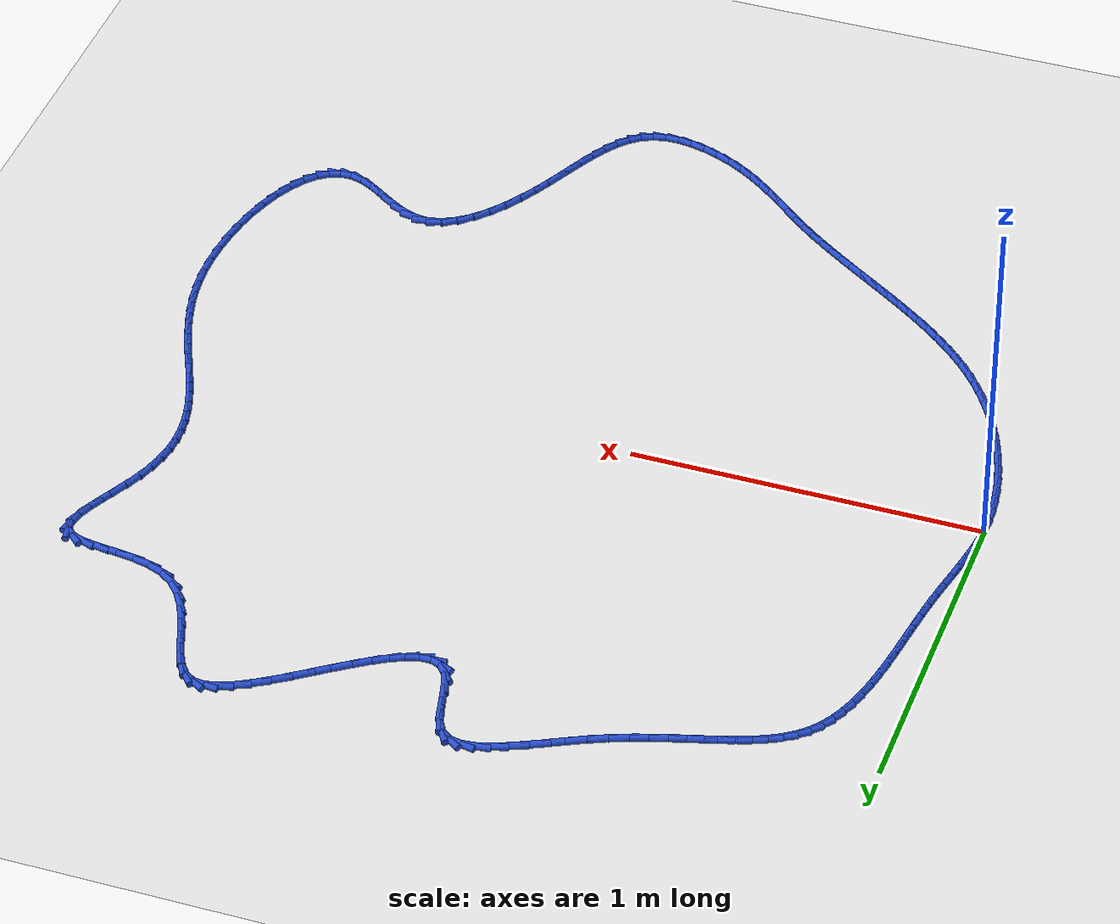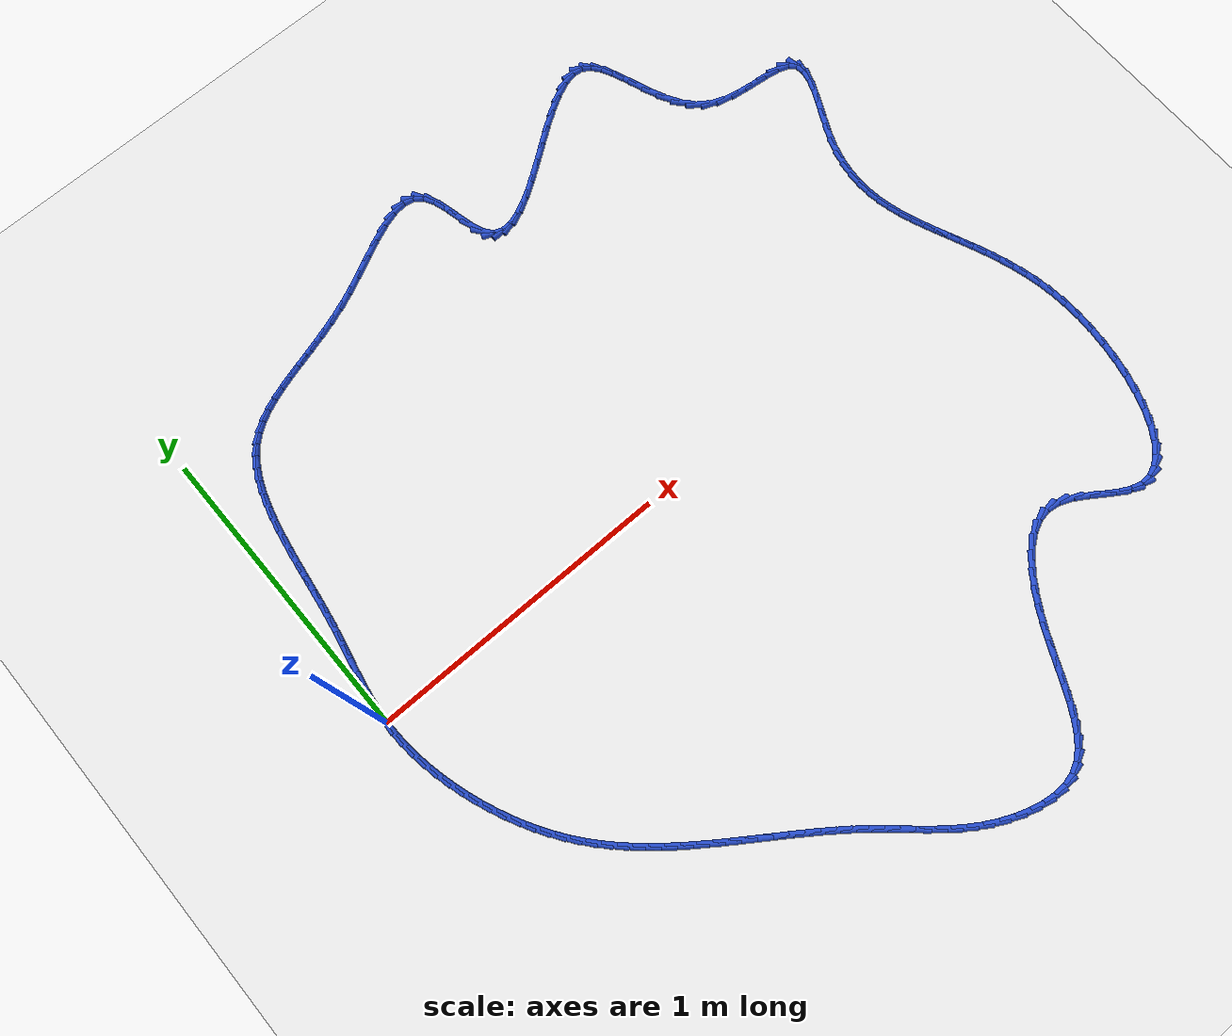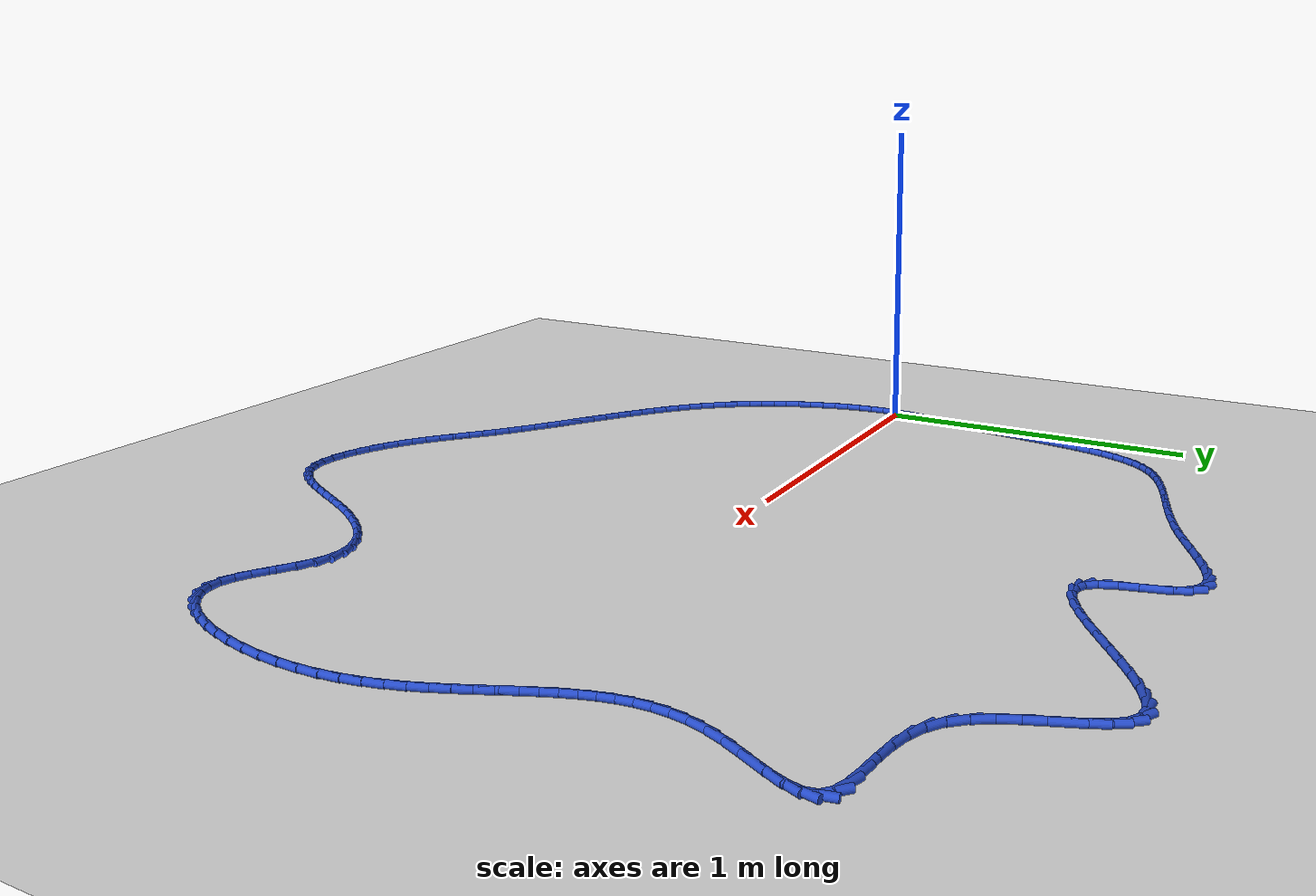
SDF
<sdf version="1.6">
 <world name="default">
  <light name="sun" type="directional">
   <pose>0 0 10 0 -0 0</pose>
   <diffuse>0.8 0.8 0.8 1</diffuse>
   <specular>0.2 0.2 0.2 1</specular>
   <attenuation>
    <range>1000</range>
    <constant>0.9</constant>
    <linear>0.01</linear>
    <quadratic>0.001</quadratic>
   </attenuation>
   <direction>-0.5 0.1 -0.9</direction>
  </light>
  <model name="ground_plane">
   <static>1</static>
   <link name="link">
    <collision name="collision">
     <geometry><plane><normal>0 0 1</normal><size>100 100</size></plane></geometry>
     <surface><friction><ode><mu>100</mu><mu2>50</mu2></ode></friction></surface>
    </collision>
    <visual name="visual">
     <cast_shadows>0</cast_shadows>
     <geometry><plane><normal>0 0 1</normal><size>100 100</size></plane></geometry>
     <material>
      <script><uri>file://media/materials/scripts/gazebo.material</uri><name>Gazebo/WhiteGlow</name></script>
     </material>
    </visual>
   </link>
  </model>
  <gravity>0 0 -9.8</gravity>
  <magnetic_field>6e-06 2.3e-05 -4.2e-05</magnetic_field>
  <atmosphere type="adiabatic"/>
  <physics name="default_physics" default="0" type="ode">
   <max_step_size>0.001</max_step_size>
   <real_time_factor>1</real_time_factor>
   <real_time_update_rate>1000</real_time_update_rate>
  </physics>
  <scene><ambient>0.4 0.4 0.4 1</ambient><background>0.7 0.7 0.7 1</background><shadows>1</shadows></scene>
  <spherical_coordinates>
   <surface_model>EARTH_WGS84</surface_model>
   <latitude_deg>0</latitude_deg>
   <longitude_deg>0</longitude_deg>
   <elevation>0</elevation>
   <heading_deg>0</heading_deg>
  </spherical_coordinates>
  <model name="line">
   <link name="link_0">
    <pose>2.7755575615628914e-17 -2.0816681711721685e-17 0.01 0 1.57 1.5020953391786414</pose>
    <collision name="collision">
     <geometry><cylinder><radius>0.01</radius><length>0.08</length></cylinder></geometry>
    </collision>
    <visual name="visual">
     <material>
      <script><name>Gazebo/Blue</name><uri>file://media/materials/scripts/gazebo.material</uri></script>
     </material>
     <geometry><cylinder><radius>0.01</radius><length>0.08</length></cylinder></geometry>
    </visual>
   </link>
   <link name="link_1">
    <pose>0.003000123174723722 0.04360056199078417 0.01 0 1.57 1.4487719705072435</pose>
    <collision name="collision">
     <geometry><cylinder><radius>0.01</radius><length>0.08</length></cylinder></geometry>
    </collision>
    <visual name="visual">
     <material>
      <script><name>Gazebo/Blue</name><uri>file://media/materials/scripts/gazebo.material</uri></script>
     </material>
     <geometry><cylinder><radius>0.01</radius><length>0.08</length></cylinder></geometry>
    </visual>
   </link>
   <link name="link_2">
    <pose>0.008314937787957541 0.08693952689009236 0.01 0 1.57 1.4082826827325916</pose>
    <collision name="collision">
     <geometry><cylinder><radius>0.01</radius><length>0.08</length></cylinder></geometry>
    </collision>
    <visual name="visual">
     <material>
      <script><name>Gazebo/Blue</name><uri>file://media/materials/scripts/gazebo.material</uri></script>
     </material>
     <geometry><cylinder><radius>0.01</radius><length>0.08</length></cylinder></geometry>
    </visual>
   </link>
   <link name="link_3">
    <pose>0.01541908743098577 0.13026818073630764 0.01 0 1.57 1.3810436912425075</pose>
    <collision name="collision">
     <geometry><cylinder><radius>0.01</radius><length>0.08</length></cylinder></geometry>
    </collision>
    <visual name="visual">
     <material>
      <script><name>Gazebo/Blue</name><uri>file://media/materials/scripts/gazebo.material</uri></script>
     </material>
     <geometry><cylinder><radius>0.01</radius><length>0.08</length></cylinder></geometry>
    </visual>
   </link>
   <link name="link_4">
    <pose>0.023787215695092654 0.17383780956781278 0.01 0 1.57 1.3669851679821063</pose>
    <collision name="collision">
     <geometry><cylinder><radius>0.01</radius><length>0.08</length></cylinder></geometry>
    </collision>
    <visual name="visual">
     <material>
      <script><name>Gazebo/Blue</name><uri>file://media/materials/scripts/gazebo.material</uri></script>
     </material>
     <geometry><cylinder><radius>0.01</radius><length>0.08</length></cylinder></geometry>
    </visual>
   </link>
   <link name="link_5">
    <pose>0.032893966171562504 0.21789969942299098 0.01 0 1.57 1.3657100421632793</pose>
    <collision name="collision">
     <geometry><cylinder><radius>0.01</radius><length>0.08</length></cylinder></geometry>
    </collision>
    <visual name="visual">
     <material>
      <script><name>Gazebo/Blue</name><uri>file://media/materials/scripts/gazebo.material</uri></script>
     </material>
     <geometry><cylinder><radius>0.01</radius><length>0.08</length></cylinder></geometry>
    </visual>
   </link>
   <link name="link_6">
    <pose>0.04221398245167956 0.26270513634022497 0.01 0 1.57 1.376596604798035</pose>
    <collision name="collision">
     <geometry><cylinder><radius>0.01</radius><length>0.08</length></cylinder></geometry>
    </collision>
    <visual name="visual">
     <material>
      <script><name>Gazebo/Blue</name><uri>file://media/materials/scripts/gazebo.material</uri></script>
     </material>
     <geometry><cylinder><radius>0.01</radius><length>0.08</length></cylinder></geometry>
    </visual>
   </link>
   <link name="link_7">
    <pose>0.051221908126728076 0.30850540635789764 0.01 0 1.57 1.3979150797331559</pose>
    <collision name="collision">
     <geometry><cylinder><radius>0.01</radius><length>0.08</length></cylinder></geometry>
    </collision>
    <visual name="visual">
     <material>
      <script><name>Gazebo/Blue</name><uri>file://media/materials/scripts/gazebo.material</uri></script>
     </material>
     <geometry><cylinder><radius>0.01</radius><length>0.08</length></cylinder></geometry>
    </visual>
   </link>
   <link name="link_8">
    <pose>0.059432024490481364 0.3555212545765996 0.01 0 1.57 1.4178376785264464</pose>
    <collision name="collision">
     <geometry><cylinder><radius>0.01</radius><length>0.08</length></cylinder></geometry>
    </collision>
    <visual name="visual">
     <material>
      <script><name>Gazebo/Blue</name><uri>file://media/materials/scripts/gazebo.material</uri></script>
     </material>
     <geometry><cylinder><radius>0.01</radius><length>0.08</length></cylinder></geometry>
    </visual>
   </link>
   <link name="link_9">
    <pose>0.06684390325323464 0.4035995087532891 0.01 0 1.57 1.4293835000493798</pose>
    <collision name="collision">
     <geometry><cylinder><radius>0.01</radius><length>0.08</length></cylinder></geometry>
    </collision>
    <visual name="visual">
     <material>
      <script><name>Gazebo/Blue</name><uri>file://media/materials/scripts/gazebo.material</uri></script>
     </material>
     <geometry><cylinder><radius>0.01</radius><length>0.08</length></cylinder></geometry>
    </visual>
   </link>
   <link name="link_10">
    <pose>0.07378224819039644 0.4523364816667232 0.01 0 1.57 1.4329565929533143</pose>
    <collision name="collision">
     <geometry><cylinder><radius>0.01</radius><length>0.08</length></cylinder></geometry>
    </collision>
    <visual name="visual">
     <material>
      <script><name>Gazebo/Blue</name><uri>file://media/materials/scripts/gazebo.material</uri></script>
     </material>
     <geometry><cylinder><radius>0.01</radius><length>0.08</length></cylinder></geometry>
    </visual>
   </link>
   <link name="link_11">
    <pose>0.08057774955936517 0.5013238734979911 0.01 0 1.57 1.4287446648675308</pose>
    <collision name="collision">
     <geometry><cylinder><radius>0.01</radius><length>0.08</length></cylinder></geometry>
    </collision>
    <visual name="visual">
     <material>
      <script><name>Gazebo/Blue</name><uri>file://media/materials/scripts/gazebo.material</uri></script>
     </material>
     <geometry><cylinder><radius>0.01</radius><length>0.08</length></cylinder></geometry>
    </visual>
   </link>
   <link name="link_12">
    <pose>0.08756109761753912 0.5501533844281816 0.01 0 1.57 1.4165937577329126</pose>
    <collision name="collision">
     <geometry><cylinder><radius>0.01</radius><length>0.08</length></cylinder></geometry>
    </collision>
    <visual name="visual">
     <material>
      <script><name>Gazebo/Blue</name><uri>file://media/materials/scripts/gazebo.material</uri></script>
     </material>
     <geometry><cylinder><radius>0.01</radius><length>0.08</length></cylinder></geometry>
    </visual>
   </link>
   <link name="link_13">
    <pose>0.09506298262231673 0.598416714638384 0.01 0 1.57 1.3960006500941866</pose>
    <collision name="collision">
     <geometry><cylinder><radius>0.01</radius><length>0.08</length></cylinder></geometry>
    </collision>
    <visual name="visual">
     <material>
      <script><name>Gazebo/Blue</name><uri>file://media/materials/scripts/gazebo.material</uri></script>
     </material>
     <geometry><cylinder><radius>0.01</radius><length>0.08</length></cylinder></geometry>
    </visual>
   </link>
   <link name="link_14">
    <pose>0.10341409483109637 0.6457055643096872 0.01 0 1.57 1.3660844540535957</pose>
    <collision name="collision">
     <geometry><cylinder><radius>0.01</radius><length>0.08</length></cylinder></geometry>
    </collision>
    <visual name="visual">
     <material>
      <script><name>Gazebo/Blue</name><uri>file://media/materials/scripts/gazebo.material</uri></script>
     </material>
     <geometry><cylinder><radius>0.01</radius><length>0.08</length></cylinder></geometry>
    </visual>
   </link>
   <link name="link_15">
    <pose>0.11294512450127644 0.6916116336231806 0.01 0 1.57 1.3255426771105276</pose>
    <collision name="collision">
     <geometry><cylinder><radius>0.01</radius><length>0.08</length></cylinder></geometry>
    </collision>
    <visual name="visual">
     <material>
      <script><name>Gazebo/Blue</name><uri>file://media/materials/scripts/gazebo.material</uri></script>
     </material>
     <geometry><cylinder><radius>0.01</radius><length>0.08</length></cylinder></geometry>
    </visual>
   </link>
   <link name="link_16">
    <pose>0.12398676189025537 0.7357266227599535 0.01 0 1.57 1.2726063591634946</pose>
    <collision name="collision">
     <geometry><cylinder><radius>0.01</radius><length>0.08</length></cylinder></geometry>
    </collision>
    <visual name="visual">
     <material>
      <script><name>Gazebo/Blue</name><uri>file://media/materials/scripts/gazebo.material</uri></script>
     </material>
     <geometry><cylinder><radius>0.01</radius><length>0.08</length></cylinder></geometry>
    </visual>
   </link>
   <link name="link_17">
    <pose>0.13686969725543144 0.7776422319010944 0.01 0 1.57 1.205030766401061</pose>
    <collision name="collision">
     <geometry><cylinder><radius>0.01</radius><length>0.08</length></cylinder></geometry>
    </collision>
    <visual name="visual">
     <material>
      <script><name>Gazebo/Blue</name><uri>file://media/materials/scripts/gazebo.material</uri></script>
     </material>
     <geometry><cylinder><radius>0.01</radius><length>0.08</length></cylinder></geometry>
    </visual>
   </link>
   <link name="link_18">
    <pose>0.1519246208542031 0.8169501612276928 0.01 0 1.57 1.1202024017794339</pose>
    <collision name="collision">
     <geometry><cylinder><radius>0.01</radius><length>0.08</length></cylinder></geometry>
    </collision>
    <visual name="visual">
     <material>
      <script><name>Gazebo/Blue</name><uri>file://media/materials/scripts/gazebo.material</uri></script>
     </material>
     <geometry><cylinder><radius>0.01</radius><length>0.08</length></cylinder></geometry>
    </visual>
   </link>
   <link name="link_19">
    <pose>0.16948222294396872 0.8532421109208379 0.01 0 1.57 1.0155146124670285</pose>
    <collision name="collision">
     <geometry><cylinder><radius>0.01</radius><length>0.08</length></cylinder></geometry>
    </collision>
    <visual name="visual">
     <material>
      <script><name>Gazebo/Blue</name><uri>file://media/materials/scripts/gazebo.material</uri></script>
     </material>
     <geometry><cylinder><radius>0.01</radius><length>0.08</length></cylinder></geometry>
    </visual>
   </link>
   <link name="link_20">
    <pose>0.1898731937821267 0.8861097811616185 0.01 0 1.57 0.8892266930254814</pose>
    <collision name="collision">
     <geometry><cylinder><radius>0.01</radius><length>0.08</length></cylinder></geometry>
    </collision>
    <visual name="visual">
     <material>
      <script><name>Gazebo/Blue</name><uri>file://media/materials/scripts/gazebo.material</uri></script>
     </material>
     <geometry><cylinder><radius>0.01</radius><length>0.08</length></cylinder></geometry>
    </visual>
   </link>
   <link name="link_21">
    <pose>0.21342822351657387 0.9151448723425092 0.01 0 1.57 0.747249347389595</pose>
    <collision name="collision">
     <geometry><cylinder><radius>0.01</radius><length>0.08</length></cylinder></geometry>
    </collision>
    <visual name="visual">
     <material>
      <script><name>Gazebo/Blue</name><uri>file://media/materials/scripts/gazebo.material</uri></script>
     </material>
     <geometry><cylinder><radius>0.01</radius><length>0.08</length></cylinder></geometry>
    </visual>
   </link>
   <link name="link_22">
    <pose>0.24038466947601064 0.9401192569875847 0.01 0 1.57 0.6155932877091566</pose>
    <collision name="collision">
     <geometry><cylinder><radius>0.01</radius><length>0.08</length></cylinder></geometry>
    </collision>
    <visual name="visual">
     <material>
      <script><name>Gazebo/Blue</name><uri>file://media/materials/scripts/gazebo.material</uri></script>
     </material>
     <geometry><cylinder><radius>0.01</radius><length>0.08</length></cylinder></geometry>
    </visual>
   </link>
   <link name="link_23">
    <pose>0.2706183057251787 0.9615028174740483 0.01 0 1.57 0.5055402793163776</pose>
    <collision name="collision">
     <geometry><cylinder><radius>0.01</radius><length>0.08</length></cylinder></geometry>
    </collision>
    <visual name="visual">
     <material>
      <script><name>Gazebo/Blue</name><uri>file://media/materials/scripts/gazebo.material</uri></script>
     </material>
     <geometry><cylinder><radius>0.01</radius><length>0.08</length></cylinder></geometry>
    </visual>
   </link>
   <link name="link_24">
    <pose>0.30391735566333544 0.9799344462889344 0.01 0 1.57 0.4193954468462097</pose>
    <collision name="collision">
     <geometry><cylinder><radius>0.01</radius><length>0.08</length></cylinder></geometry>
    </collision>
    <visual name="visual">
     <material>
      <script><name>Gazebo/Blue</name><uri>file://media/materials/scripts/gazebo.material</uri></script>
     </material>
     <geometry><cylinder><radius>0.01</radius><length>0.08</length></cylinder></geometry>
    </visual>
   </link>
   <link name="link_25">
    <pose>0.3400700426897386 0.9960530359192789 0.01 0 1.57 0.35642935938417514</pose>
    <collision name="collision">
     <geometry><cylinder><radius>0.01</radius><length>0.08</length></cylinder></geometry>
    </collision>
    <visual name="visual">
     <material>
      <script><name>Gazebo/Blue</name><uri>file://media/materials/scripts/gazebo.material</uri></script>
     </material>
     <geometry><cylinder><radius>0.01</radius><length>0.08</length></cylinder></geometry>
    </visual>
   </link>
   <link name="link_26">
    <pose>0.3788645902036459 1.0104974788521168 0.01 0 1.57 0.31447724517197523</pose>
    <collision name="collision">
     <geometry><cylinder><radius>0.01</radius><length>0.08</length></cylinder></geometry>
    </collision>
    <visual name="visual">
     <material>
      <script><name>Gazebo/Blue</name><uri>file://media/materials/scripts/gazebo.material</uri></script>
     </material>
     <geometry><cylinder><radius>0.01</radius><length>0.08</length></cylinder></geometry>
    </visual>
   </link>
   <link name="link_27">
    <pose>0.42008922160431506 1.0239066675744843 0.01 0 1.57 0.2910332260113002</pose>
    <collision name="collision">
     <geometry><cylinder><radius>0.01</radius><length>0.08</length></cylinder></geometry>
    </collision>
    <visual name="visual">
     <material>
      <script><name>Gazebo/Blue</name><uri>file://media/materials/scripts/gazebo.material</uri></script>
     </material>
     <geometry><cylinder><radius>0.01</radius><length>0.08</length></cylinder></geometry>
    </visual>
   </link>
   <link name="link_28">
    <pose>0.4635321602910032 1.0369194945734155 0.01 0 1.57 0.2837791551019473</pose>
    <collision name="collision">
     <geometry><cylinder><radius>0.01</radius><length>0.08</length></cylinder></geometry>
    </collision>
    <visual name="visual">
     <material>
      <script><name>Gazebo/Blue</name><uri>file://media/materials/scripts/gazebo.material</uri></script>
     </material>
     <geometry><cylinder><radius>0.01</radius><length>0.08</length></cylinder></geometry>
    </visual>
   </link>
   <link name="link_29">
    <pose>0.5089816296629687 1.0501748523359467 0.01 0 1.57 0.2907481252536444</pose>
    <collision name="collision">
     <geometry><cylinder><radius>0.01</radius><length>0.08</length></cylinder></geometry>
    </collision>
    <visual name="visual">
     <material>
      <script><name>Gazebo/Blue</name><uri>file://media/materials/scripts/gazebo.material</uri></script>
     </material>
     <geometry><cylinder><radius>0.01</radius><length>0.08</length></cylinder></geometry>
    </visual>
   </link>
   <link name="link_30">
    <pose>0.5562258531194686 1.0643116333491127 0.01 0 1.57 0.3103046155513398</pose>
    <collision name="collision">
     <geometry><cylinder><radius>0.01</radius><length>0.08</length></cylinder></geometry>
    </collision>
    <visual name="visual">
     <material>
      <script><name>Gazebo/Blue</name><uri>file://media/materials/scripts/gazebo.material</uri></script>
     </material>
     <geometry><cylinder><radius>0.01</radius><length>0.08</length></cylinder></geometry>
    </visual>
   </link>
   <link name="link_31">
    <pose>0.605053054059761 1.0799687300999492 0.01 0 1.57 0.3410491732848912</pose>
    <collision name="collision">
     <geometry><cylinder><radius>0.01</radius><length>0.08</length></cylinder></geometry>
    </collision>
    <visual name="visual">
     <material>
      <script><name>Gazebo/Blue</name><uri>file://media/materials/scripts/gazebo.material</uri></script>
     </material>
     <geometry><cylinder><radius>0.01</radius><length>0.08</length></cylinder></geometry>
    </visual>
   </link>
   <link name="link_32">
    <pose>0.655251455883103 1.0977850350754914 0.01 0 1.57 0.3817021979175472</pose>
    <collision name="collision">
     <geometry><cylinder><radius>0.01</radius><length>0.08</length></cylinder></geometry>
    </collision>
    <visual name="visual">
     <material>
      <script><name>Gazebo/Blue</name><uri>file://media/materials/scripts/gazebo.material</uri></script>
     </material>
     <geometry><cylinder><radius>0.01</radius><length>0.08</length></cylinder></geometry>
    </visual>
   </link>
   <link name="link_33">
    <pose>0.7066092819887524 1.1183994407627744 0.01 0 1.57 0.4292885203098368</pose>
    <collision name="collision">
     <geometry><cylinder><radius>0.01</radius><length>0.08</length></cylinder></geometry>
    </collision>
    <visual name="visual">
     <material>
      <script><name>Gazebo/Blue</name><uri>file://media/materials/scripts/gazebo.material</uri></script>
     </material>
     <geometry><cylinder><radius>0.01</radius><length>0.08</length></cylinder></geometry>
    </visual>
   </link>
   <link name="link_34">
    <pose>0.7588811510512592 1.142327420781965 0.01 0 1.57 0.46237842196865514</pose>
    <collision name="collision">
     <geometry><cylinder><radius>0.01</radius><length>0.08</length></cylinder></geometry>
    </collision>
    <visual name="visual">
     <material>
      <script><name>Gazebo/Blue</name><uri>file://media/materials/scripts/gazebo.material</uri></script>
     </material>
     <geometry><cylinder><radius>0.01</radius><length>0.08</length></cylinder></geometry>
    </visual>
   </link>
   <link name="link_35">
    <pose>0.8113898635616469 1.1684985256020368 0.01 0 1.57 0.4691872814323697</pose>
    <collision name="collision">
     <geometry><cylinder><radius>0.01</radius><length>0.08</length></cylinder></geometry>
    </collision>
    <visual name="visual">
     <material>
      <script><name>Gazebo/Blue</name><uri>file://media/materials/scripts/gazebo.material</uri></script>
     </material>
     <geometry><cylinder><radius>0.01</radius><length>0.08</length></cylinder></geometry>
    </visual>
   </link>
   <link name="link_36">
    <pose>0.8631587479808225 1.194742445510482 0.01 0 1.57 0.4491761531706543</pose>
    <collision name="collision">
     <geometry><cylinder><radius>0.01</radius><length>0.08</length></cylinder></geometry>
    </collision>
    <visual name="visual">
     <material>
      <script><name>Gazebo/Blue</name><uri>file://media/materials/scripts/gazebo.material</uri></script>
     </material>
     <geometry><cylinder><radius>0.01</radius><length>0.08</length></cylinder></geometry>
    </visual>
   </link>
   <link name="link_37">
    <pose>0.9132051137208044 1.218866764849879 0.01 0 1.57 0.3963527560962091</pose>
    <collision name="collision">
     <geometry><cylinder><radius>0.01</radius><length>0.08</length></cylinder></geometry>
    </collision>
    <visual name="visual">
     <material>
      <script><name>Gazebo/Blue</name><uri>file://media/materials/scripts/gazebo.material</uri></script>
     </material>
     <geometry><cylinder><radius>0.01</radius><length>0.08</length></cylinder></geometry>
    </visual>
   </link>
   <link name="link_38">
    <pose>0.9605462701936123 1.2386790679628068 0.01 0 1.57 0.295904062783631</pose>
    <collision name="collision">
     <geometry><cylinder><radius>0.01</radius><length>0.08</length></cylinder></geometry>
    </collision>
    <visual name="visual">
     <material>
      <script><name>Gazebo/Blue</name><uri>file://media/materials/scripts/gazebo.material</uri></script>
     </material>
     <geometry><cylinder><radius>0.01</radius><length>0.08</length></cylinder></geometry>
    </visual>
   </link>
   <link name="link_39">
    <pose>1.0041995268112665 1.2519869391918461 0.01 0 1.57 0.11773689323920024</pose>
    <collision name="collision">
     <geometry><cylinder><radius>0.01</radius><length>0.08</length></cylinder></geometry>
    </collision>
    <visual name="visual">
     <material>
      <script><name>Gazebo/Blue</name><uri>file://media/materials/scripts/gazebo.material</uri></script>
     </material>
     <geometry><cylinder><radius>0.01</radius><length>0.08</length></cylinder></geometry>
    </visual>
   </link>
   <link name="link_40">
    <pose>1.0431821929857856 1.2565979628795751 0.01 0 1.57 -0.18618778433315314</pose>
    <collision name="collision">
     <geometry><cylinder><radius>0.01</radius><length>0.08</length></cylinder></geometry>
    </collision>
    <visual name="visual">
     <material>
      <script><name>Gazebo/Blue</name><uri>file://media/materials/scripts/gazebo.material</uri></script>
     </material>
     <geometry><cylinder><radius>0.01</radius><length>0.08</length></cylinder></geometry>
    </visual>
   </link>
   <link name="link_41">
    <pose>1.0765115781291899 1.2503197233685737 0.01 0 1.57 -0.6274848108858475</pose>
    <collision name="collision">
     <geometry><cylinder><radius>0.01</radius><length>0.08</length></cylinder></geometry>
    </collision>
    <visual name="visual">
     <material>
      <script><name>Gazebo/Blue</name><uri>file://media/materials/scripts/gazebo.material</uri></script>
     </material>
     <geometry><cylinder><radius>0.01</radius><length>0.08</length></cylinder></geometry>
    </visual>
   </link>
   <link name="link_42">
    <pose>1.1032049916534987 1.2309598050014217 0.01 0 1.57 -1.048942900025096</pose>
    <collision name="collision">
     <geometry><cylinder><radius>0.01</radius><length>0.08</length></cylinder></geometry>
    </collision>
    <visual name="visual">
     <material>
      <script><name>Gazebo/Blue</name><uri>file://media/materials/scripts/gazebo.material</uri></script>
     </material>
     <geometry><cylinder><radius>0.01</radius><length>0.08</length></cylinder></geometry>
    </visual>
   </link>
   <link name="link_43">
    <pose>1.1226563271066412 1.1971328943556334 0.01 0 1.57 -1.2640495415212665</pose>
    <collision name="collision">
     <geometry><cylinder><radius>0.01</radius><length>0.08</length></cylinder></geometry>
    </collision>
    <visual name="visual">
     <material>
      <script><name>Gazebo/Blue</name><uri>file://media/materials/scripts/gazebo.material</uri></script>
     </material>
     <geometry><cylinder><radius>0.01</radius><length>0.08</length></cylinder></geometry>
    </visual>
   </link>
   <link name="link_44">
    <pose>1.1367209531095206 1.1527291578900865 0.01 0 1.57 -1.3397152905847816</pose>
    <collision name="collision">
     <geometry><cylinder><radius>0.01</radius><length>0.08</length></cylinder></geometry>
    </collision>
    <visual name="visual">
     <material>
      <script><name>Gazebo/Blue</name><uri>file://media/materials/scripts/gazebo.material</uri></script>
     </material>
     <geometry><cylinder><radius>0.01</radius><length>0.08</length></cylinder></geometry>
    </visual>
   </link>
   <link name="link_45">
    <pose>1.148243070122668 1.1037580451444797 0.01 0 1.57 -1.326894126529341</pose>
    <collision name="collision">
     <geometry><cylinder><radius>0.01</radius><length>0.08</length></cylinder></geometry>
    </collision>
    <visual name="visual">
     <material>
      <script><name>Gazebo/Blue</name><uri>file://media/materials/scripts/gazebo.material</uri></script>
     </material>
     <geometry><cylinder><radius>0.01</radius><length>0.08</length></cylinder></geometry>
    </visual>
   </link>
   <link name="link_46">
    <pose>1.1600695557725238 1.056234743411067 0.01 0 1.57 -1.2130082496170382</pose>
    <collision name="collision">
     <geometry><cylinder><radius>0.01</radius><length>0.08</length></cylinder></geometry>
    </collision>
    <visual name="visual">
     <material>
      <script><name>Gazebo/Blue</name><uri>file://media/materials/scripts/gazebo.material</uri></script>
     </material>
     <geometry><cylinder><radius>0.01</radius><length>0.08</length></cylinder></geometry>
    </visual>
   </link>
   <link name="link_47">
    <pose>1.1750472876855285 1.016174439982104 0.01 0 1.57 -0.9089546877038118</pose>
    <collision name="collision">
     <geometry><cylinder><radius>0.01</radius><length>0.08</length></cylinder></geometry>
    </collision>
    <visual name="visual">
     <material>
      <script><name>Gazebo/Blue</name><uri>file://media/materials/scripts/gazebo.material</uri></script>
     </material>
     <geometry><cylinder><radius>0.01</radius><length>0.08</length></cylinder></geometry>
    </visual>
   </link>
   <link name="link_48">
    <pose>1.1959233011310941 0.9893780294693962 0.01 0 1.57 -0.40412909897627924</pose>
    <collision name="collision">
     <geometry><cylinder><radius>0.01</radius><length>0.08</length></cylinder></geometry>
    </collision>
    <visual name="visual">
     <material>
      <script><name>Gazebo/Blue</name><uri>file://media/materials/scripts/gazebo.material</uri></script>
     </material>
     <geometry><cylinder><radius>0.01</radius><length>0.08</length></cylinder></geometry>
    </visual>
   </link>
   <link name="link_49">
    <pose>1.2235433987558428 0.9775657713012891 0.01 0 1.57 0.036799329950371704</pose>
    <collision name="collision">
     <geometry><cylinder><radius>0.01</radius><length>0.08</length></cylinder></geometry>
    </collision>
    <visual name="visual">
     <material>
      <script><name>Gazebo/Blue</name><uri>file://media/materials/scripts/gazebo.material</uri></script>
     </material>
     <geometry><cylinder><radius>0.01</radius><length>0.08</length></cylinder></geometry>
    </visual>
   </link>
   <link name="link_50">
    <pose>1.2570487734947093 0.9787993035042969 0.01 0 1.57 0.3073554351599127</pose>
    <collision name="collision">
     <geometry><cylinder><radius>0.01</radius><length>0.08</length></cylinder></geometry>
    </collision>
    <visual name="visual">
     <material>
      <script><name>Gazebo/Blue</name><uri>file://media/materials/scripts/gazebo.material</uri></script>
     </material>
     <geometry><cylinder><radius>0.01</radius><length>0.08</length></cylinder></geometry>
    </visual>
   </link>
   <link name="link_51">
    <pose>1.2955202474756615 0.9910106896194093 0.01 0 1.57 0.46104971388925536</pose>
    <collision name="collision">
     <geometry><cylinder><radius>0.01</radius><length>0.08</length></cylinder></geometry>
    </collision>
    <visual name="visual">
     <material>
      <script><name>Gazebo/Blue</name><uri>file://media/materials/scripts/gazebo.material</uri></script>
     </material>
     <geometry><cylinder><radius>0.01</radius><length>0.08</length></cylinder></geometry>
    </visual>
   </link>
   <link name="link_52">
    <pose>1.3380386428266666 1.0121319931876152 0.01 0 1.57 0.5496400553464482</pose>
    <collision name="collision">
     <geometry><cylinder><radius>0.01</radius><length>0.08</length></cylinder></geometry>
    </collision>
    <visual name="visual">
     <material>
      <script><name>Gazebo/Blue</name><uri>file://media/materials/scripts/gazebo.material</uri></script>
     </material>
     <geometry><cylinder><radius>0.01</radius><length>0.08</length></cylinder></geometry>
    </visual>
   </link>
   <link name="link_53">
    <pose>1.3836847816756912 1.0400952777499033 0.01 0 1.57 0.5999738697980465</pose>
    <collision name="collision">
     <geometry><cylinder><radius>0.01</radius><length>0.08</length></cylinder></geometry>
    </collision>
    <visual name="visual">
     <material>
      <script><name>Gazebo/Blue</name><uri>file://media/materials/scripts/gazebo.material</uri></script>
     </material>
     <geometry><cylinder><radius>0.01</radius><length>0.08</length></cylinder></geometry>
    </visual>
   </link>
   <link name="link_54">
    <pose>1.4315394861507045 1.0728326068472644 0.01 0 1.57 0.6248225180725825</pose>
    <collision name="collision">
     <geometry><cylinder><radius>0.01</radius><length>0.08</length></cylinder></geometry>
    </collision>
    <visual name="visual">
     <material>
      <script><name>Gazebo/Blue</name><uri>file://media/materials/scripts/gazebo.material</uri></script>
     </material>
     <geometry><cylinder><radius>0.01</radius><length>0.08</length></cylinder></geometry>
    </visual>
   </link>
   <link name="link_55">
    <pose>1.4806835783796732 1.1082760440206874 0.01 0 1.57 0.6297362480089207</pose>
    <collision name="collision">
     <geometry><cylinder><radius>0.01</radius><length>0.08</length></cylinder></geometry>
    </collision>
    <visual name="visual">
     <material>
      <script><name>Gazebo/Blue</name><uri>file://media/materials/scripts/gazebo.material</uri></script>
     </material>
     <geometry><cylinder><radius>0.01</radius><length>0.08</length></cylinder></geometry>
    </visual>
   </link>
   <link name="link_56">
    <pose>1.530197880490564 1.1443576528111603 0.01 0 1.57 0.6158625173784111</pose>
    <collision name="collision">
     <geometry><cylinder><radius>0.01</radius><length>0.08</length></cylinder></geometry>
    </collision>
    <visual name="visual">
     <material>
      <script><name>Gazebo/Blue</name><uri>file://media/materials/scripts/gazebo.material</uri></script>
     </material>
     <geometry><cylinder><radius>0.01</radius><length>0.08</length></cylinder></geometry>
    </visual>
   </link>
   <link name="link_57">
    <pose>1.5791632146113457 1.179009496759674 0.01 0 1.57 0.5805225199326179</pose>
    <collision name="collision">
     <geometry><cylinder><radius>0.01</radius><length>0.08</length></cylinder></geometry>
    </collision>
    <visual name="visual">
     <material>
      <script><name>Gazebo/Blue</name><uri>file://media/materials/scripts/gazebo.material</uri></script>
     </material>
     <geometry><cylinder><radius>0.01</radius><length>0.08</length></cylinder></geometry>
    </visual>
   </link>
   <link name="link_58">
    <pose>1.6266604028699856 1.210163639407217 0.01 0 1.57 0.5159893415369324</pose>
    <collision name="collision">
     <geometry><cylinder><radius>0.01</radius><length>0.08</length></cylinder></geometry>
    </collision>
    <visual name="visual">
     <material>
      <script><name>Gazebo/Blue</name><uri>file://media/materials/scripts/gazebo.material</uri></script>
     </material>
     <geometry><cylinder><radius>0.01</radius><length>0.08</length></cylinder></geometry>
    </visual>
   </link>
   <link name="link_59">
    <pose>1.6717702673944506 1.235752144294779 0.01 0 1.57 0.4056838068010564</pose>
    <collision name="collision">
     <geometry><cylinder><radius>0.01</radius><length>0.08</length></cylinder></geometry>
    </collision>
    <visual name="visual">
     <material>
      <script><name>Gazebo/Blue</name><uri>file://media/materials/scripts/gazebo.material</uri></script>
     </material>
     <geometry><cylinder><radius>0.01</radius><length>0.08</length></cylinder></geometry>
    </visual>
   </link>
   <link name="link_60">
    <pose>1.7135736303127085 1.2537070749633488 0.01 0 1.57 0.21620328356511367</pose>
    <collision name="collision">
     <geometry><cylinder><radius>0.01</radius><length>0.08</length></cylinder></geometry>
    </collision>
    <visual name="visual">
     <material>
      <script><name>Gazebo/Blue</name><uri>file://media/materials/scripts/gazebo.material</uri></script>
     </material>
     <geometry><cylinder><radius>0.01</radius><length>0.08</length></cylinder></geometry>
    </visual>
   </link>
   <link name="link_61">
    <pose>1.7511513137527273 1.2619604949539165 0.01 0 1.57 -0.10798779225799847</pose>
    <collision name="collision">
     <geometry><cylinder><radius>0.01</radius><length>0.08</length></cylinder></geometry>
    </collision>
    <visual name="visual">
     <material>
      <script><name>Gazebo/Blue</name><uri>file://media/materials/scripts/gazebo.material</uri></script>
     </material>
     <geometry><cylinder><radius>0.01</radius><length>0.08</length></cylinder></geometry>
    </visual>
   </link>
   <link name="link_62">
    <pose>1.7835841398424739 1.2584444678074707 0.01 0 1.57 -0.557595516058612</pose>
    <collision name="collision">
     <geometry><cylinder><radius>0.01</radius><length>0.08</length></cylinder></geometry>
    </collision>
    <visual name="visual">
     <material>
      <script><name>Gazebo/Blue</name><uri>file://media/materials/scripts/gazebo.material</uri></script>
     </material>
     <geometry><cylinder><radius>0.01</radius><length>0.08</length></cylinder></geometry>
    </visual>
   </link>
   <link name="link_63">
    <pose>1.8103151618089077 1.2417748697533397 0.01 0 1.57 -0.9047620182827019</pose>
    <collision name="collision">
     <geometry><cylinder><radius>0.01</radius><length>0.08</length></cylinder></geometry>
    </collision>
    <visual name="visual">
     <material>
      <script><name>Gazebo/Blue</name><uri>file://media/materials/scripts/gazebo.material</uri></script>
     </material>
     <geometry><cylinder><radius>0.01</radius><length>0.08</length></cylinder></geometry>
    </visual>
   </link>
   <link name="link_64">
    <pose>1.8324186401709102 1.213646937811873 0.01 0 1.57 -1.0964707608126696</pose>
    <collision name="collision">
     <geometry><cylinder><radius>0.01</radius><length>0.08</length></cylinder></geometry>
    </collision>
    <visual name="visual">
     <material>
      <script><name>Gazebo/Blue</name><uri>file://media/materials/scripts/gazebo.material</uri></script>
     </material>
     <geometry><cylinder><radius>0.01</radius><length>0.08</length></cylinder></geometry>
    </visual>
   </link>
   <link name="link_65">
    <pose>1.8514277989776242 1.176622331258031 0.01 0 1.57 -1.188218814374237</pose>
    <collision name="collision">
     <geometry><cylinder><radius>0.01</radius><length>0.08</length></cylinder></geometry>
    </collision>
    <visual name="visual">
     <material>
      <script><name>Gazebo/Blue</name><uri>file://media/materials/scripts/gazebo.material</uri></script>
     </material>
     <geometry><cylinder><radius>0.01</radius><length>0.08</length></cylinder></geometry>
    </visual>
   </link>
   <link name="link_66">
    <pose>1.8688758873999156 1.1332627567910643 0.01 0 1.57 -1.2167688260986915</pose>
    <collision name="collision">
     <geometry><cylinder><radius>0.01</radius><length>0.08</length></cylinder></geometry>
    </collision>
    <visual name="visual">
     <material>
      <script><name>Gazebo/Blue</name><uri>file://media/materials/scripts/gazebo.material</uri></script>
     </material>
     <geometry><cylinder><radius>0.01</radius><length>0.08</length></cylinder></geometry>
    </visual>
   </link>
   <link name="link_67">
    <pose>1.8862961546086505 1.0861299211102216 0.01 0 1.57 -1.1976592762950615</pose>
    <collision name="collision">
     <geometry><cylinder><radius>0.01</radius><length>0.08</length></cylinder></geometry>
    </collision>
    <visual name="visual">
     <material>
      <script><name>Gazebo/Blue</name><uri>file://media/materials/scripts/gazebo.material</uri></script>
     </material>
     <geometry><cylinder><radius>0.01</radius><length>0.08</length></cylinder></geometry>
    </visual>
   </link>
   <link name="link_68">
    <pose>1.9052218497746969 1.0377855309147541 0.01 0 1.57 -1.1335799747302893</pose>
    <collision name="collision">
     <geometry><cylinder><radius>0.01</radius><length>0.08</length></cylinder></geometry>
    </collision>
    <visual name="visual">
     <material>
      <script><name>Gazebo/Blue</name><uri>file://media/materials/scripts/gazebo.material</uri></script>
     </material>
     <geometry><cylinder><radius>0.01</radius><length>0.08</length></cylinder></geometry>
    </visual>
   </link>
   <link name="link_69">
    <pose>1.9271862220689193 0.9907912929039119 0.01 0 1.57 -1.0187362894396148</pose>
    <collision name="collision">
     <geometry><cylinder><radius>0.01</radius><length>0.08</length></cylinder></geometry>
    </collision>
    <visual name="visual">
     <material>
      <script><name>Gazebo/Blue</name><uri>file://media/materials/scripts/gazebo.material</uri></script>
     </material>
     <geometry><cylinder><radius>0.01</radius><length>0.08</length></cylinder></geometry>
    </visual>
   </link>
   <link name="link_70">
    <pose>1.9537225206621838 0.9477089137769452 0.01 0 1.57 -0.8426254718458752</pose>
    <collision name="collision">
     <geometry><cylinder><radius>0.01</radius><length>0.08</length></cylinder></geometry>
    </collision>
    <visual name="visual">
     <material>
      <script><name>Gazebo/Blue</name><uri>file://media/materials/scripts/gazebo.material</uri></script>
     </material>
     <geometry><cylinder><radius>0.01</radius><length>0.08</length></cylinder></geometry>
    </visual>
   </link>
   <link name="link_71">
    <pose>1.9863639947253582 0.9111001002331038 0.01 0 1.57 -0.6008930600144414</pose>
    <collision name="collision">
     <geometry><cylinder><radius>0.01</radius><length>0.08</length></cylinder></geometry>
    </collision>
    <visual name="visual">
     <material>
      <script><name>Gazebo/Blue</name><uri>file://media/materials/scripts/gazebo.material</uri></script>
     </material>
     <geometry><cylinder><radius>0.01</radius><length>0.08</length></cylinder></geometry>
    </visual>
   </link>
   <link name="link_72">
    <pose>2.0266234555063716 0.8835043067539454 0.01 0 1.57 -0.3595271560284184</pose>
    <collision name="collision">
     <geometry><cylinder><radius>0.01</radius><length>0.08</length></cylinder></geometry>
    </collision>
    <visual name="visual">
     <material>
      <script><name>Gazebo/Blue</name><uri>file://media/materials/scripts/gazebo.material</uri></script>
     </material>
     <geometry><cylinder><radius>0.01</radius><length>0.08</length></cylinder></geometry>
    </visual>
   </link>
   <link name="link_73">
    <pose>2.0742926991614454 0.8655871965070105 0.01 0 1.57 -0.20598213762318981</pose>
    <collision name="collision">
     <geometry><cylinder><radius>0.01</radius><length>0.08</length></cylinder></geometry>
    </collision>
    <visual name="visual">
     <material>
      <script><name>Gazebo/Blue</name><uri>file://media/materials/scripts/gazebo.material</uri></script>
     </material>
     <geometry><cylinder><radius>0.01</radius><length>0.08</length></cylinder></geometry>
    </visual>
   </link>
   <link name="link_74">
    <pose>2.126164211874888 0.8547488709570461 0.01 0 1.57 -0.12653876003628145</pose>
    <collision name="collision">
     <geometry><cylinder><radius>0.01</radius><length>0.08</length></cylinder></geometry>
    </collision>
    <visual name="visual">
     <material>
      <script><name>Gazebo/Blue</name><uri>file://media/materials/scripts/gazebo.material</uri></script>
     </material>
     <geometry><cylinder><radius>0.01</radius><length>0.08</length></cylinder></geometry>
    </visual>
   </link>
   <link name="link_75">
    <pose>2.17872938536466 0.848061608647052 0.01 0 1.57 -0.10938864065094271</pose>
    <collision name="collision">
     <geometry><cylinder><radius>0.01</radius><length>0.08</length></cylinder></geometry>
    </collision>
    <visual name="visual">
     <material>
      <script><name>Gazebo/Blue</name><uri>file://media/materials/scripts/gazebo.material</uri></script>
     </material>
     <geometry><cylinder><radius>0.01</radius><length>0.08</length></cylinder></geometry>
    </visual>
   </link>
   <link name="link_76">
    <pose>2.228479611348723 0.8425976881200272 0.01 0 1.57 -0.16359161893482888</pose>
    <collision name="collision">
     <geometry><cylinder><radius>0.01</radius><length>0.08</length></cylinder></geometry>
    </collision>
    <visual name="visual">
     <material>
      <script><name>Gazebo/Blue</name><uri>file://media/materials/scripts/gazebo.material</uri></script>
     </material>
     <geometry><cylinder><radius>0.01</radius><length>0.08</length></cylinder></geometry>
    </visual>
   </link>
   <link name="link_77">
    <pose>2.2719062815450393 0.8354293879189704 0.01 0 1.57 -0.3377967429531294</pose>
    <collision name="collision">
     <geometry><cylinder><radius>0.01</radius><length>0.08</length></cylinder></geometry>
    </collision>
    <visual name="visual">
     <material>
      <script><name>Gazebo/Blue</name><uri>file://media/materials/scripts/gazebo.material</uri></script>
     </material>
     <geometry><cylinder><radius>0.01</radius><length>0.08</length></cylinder></geometry>
    </visual>
   </link>
   <link name="link_78">
    <pose>2.3055007876715687 0.8236289865868804 0.01 0 1.57 -0.7627459349633288</pose>
    <collision name="collision">
     <geometry><cylinder><radius>0.01</radius><length>0.08</length></cylinder></geometry>
    </collision>
    <visual name="visual">
     <material>
      <script><name>Gazebo/Blue</name><uri>file://media/materials/scripts/gazebo.material</uri></script>
     </material>
     <geometry><cylinder><radius>0.01</radius><length>0.08</length></cylinder></geometry>
    </visual>
   </link>
   <link name="link_79">
    <pose>2.3257568882500244 0.8042704004582167 0.01 0 1.57 -1.3962594613123194</pose>
    <collision name="collision">
     <geometry><cylinder><radius>0.01</radius><length>0.08</length></cylinder></geometry>
    </collision>
    <visual name="visual">
     <material>
      <script><name>Gazebo/Blue</name><uri>file://media/materials/scripts/gazebo.material</uri></script>
     </material>
     <geometry><cylinder><radius>0.01</radius><length>0.08</length></cylinder></geometry>
    </visual>
   </link>
   <link name="link_80">
    <pose>2.3308178408024744 0.7755689735743223 0.01 0 1.57 1.3702653605516295</pose>
    <collision name="collision">
     <geometry><cylinder><radius>0.01</radius><length>0.08</length></cylinder></geometry>
    </collision>
    <visual name="visual">
     <material>
      <script><name>Gazebo/Blue</name><uri>file://media/materials/scripts/gazebo.material</uri></script>
     </material>
     <geometry><cylinder><radius>0.01</radius><length>0.08</length></cylinder></geometry>
    </visual>
   </link>
   <link name="link_81">
    <pose>2.323359651814947 0.7388766419082017 0.01 0 1.57 1.2022173317868696</pose>
    <collision name="collision">
     <geometry><cylinder><radius>0.01</radius><length>0.08</length></cylinder></geometry>
    </collision>
    <visual name="visual">
     <material>
      <script><name>Gazebo/Blue</name><uri>file://media/materials/scripts/gazebo.material</uri></script>
     </material>
     <geometry><cylinder><radius>0.01</radius><length>0.08</length></cylinder></geometry>
    </visual>
   </link>
   <link name="link_82">
    <pose>2.3068301029237173 0.6960793978583469 0.01 0 1.57 1.1304684910621832</pose>
    <collision name="collision">
     <geometry><cylinder><radius>0.01</radius><length>0.08</length></cylinder></geometry>
    </collision>
    <visual name="visual">
     <material>
      <script><name>Gazebo/Blue</name><uri>file://media/materials/scripts/gazebo.material</uri></script>
     </material>
     <geometry><cylinder><radius>0.01</radius><length>0.08</length></cylinder></geometry>
    </visual>
   </link>
   <link name="link_83">
    <pose>2.284676975765059 0.6490632338232505 0.01 0 1.57 1.1127672906847215</pose>
    <collision name="collision">
     <geometry><cylinder><radius>0.01</radius><length>0.08</length></cylinder></geometry>
    </collision>
    <visual name="visual">
     <material>
      <script><name>Gazebo/Blue</name><uri>file://media/materials/scripts/gazebo.material</uri></script>
     </material>
     <geometry><cylinder><radius>0.01</radius><length>0.08</length></cylinder></geometry>
    </visual>
   </link>
   <link name="link_84">
    <pose>2.2603480519752455 0.5997141422014027 0.01 0 1.57 1.1371615496339331</pose>
    <collision name="collision">
     <geometry><cylinder><radius>0.01</radius><length>0.08</length></cylinder></geometry>
    </collision>
    <visual name="visual">
     <material>
      <script><name>Gazebo/Blue</name><uri>file://media/materials/scripts/gazebo.material</uri></script>
     </material>
     <geometry><cylinder><radius>0.01</radius><length>0.08</length></cylinder></geometry>
    </visual>
   </link>
   <link name="link_85">
    <pose>2.237291113190553 0.5499181153912958 0.01 0 1.57 1.2058650607221721</pose>
    <collision name="collision">
     <geometry><cylinder><radius>0.01</radius><length>0.08</length></cylinder></geometry>
    </collision>
    <visual name="visual">
     <material>
      <script><name>Gazebo/Blue</name><uri>file://media/materials/scripts/gazebo.material</uri></script>
     </material>
     <geometry><cylinder><radius>0.01</radius><length>0.08</length></cylinder></geometry>
    </visual>
   </link>
   <link name="link_86">
    <pose>2.2187807730781026 0.5014672183749537 0.01 0 1.57 1.3003858675052062</pose>
    <collision name="collision">
     <geometry><cylinder><radius>0.01</radius><length>0.08</length></cylinder></geometry>
    </collision>
    <visual name="visual">
     <material>
      <script><name>Gazebo/Blue</name><uri>file://media/materials/scripts/gazebo.material</uri></script>
     </material>
     <geometry><cylinder><radius>0.01</radius><length>0.08</length></cylinder></geometry>
    </visual>
   </link>
   <link name="link_87">
    <pose>2.205888566906928 0.45495855228962423 0.01 0 1.57 1.400129753790239</pose>
    <collision name="collision">
     <geometry><cylinder><radius>0.01</radius><length>0.08</length></cylinder></geometry>
    </collision>
    <visual name="visual">
     <material>
      <script><name>Gazebo/Blue</name><uri>file://media/materials/scripts/gazebo.material</uri></script>
     </material>
     <geometry><cylinder><radius>0.01</radius><length>0.08</length></cylinder></geometry>
    </visual>
   </link>
   <link name="link_88">
    <pose>2.1981689370550104 0.410166337363942 0.01 0 1.57 1.5011326419237043</pose>
    <collision name="collision">
     <geometry><cylinder><radius>0.01</radius><length>0.08</length></cylinder></geometry>
    </collision>
    <visual name="visual">
     <material>
      <script><name>Gazebo/Blue</name><uri>file://media/materials/scripts/gazebo.material</uri></script>
     </material>
     <geometry><cylinder><radius>0.01</radius><length>0.08</length></cylinder></geometry>
    </visual>
   </link>
   <link name="link_89">
    <pose>2.195146368895696 0.3668485449552015 0.01 0 1.57 -1.542314840841961</pose>
    <collision name="collision">
     <geometry><cylinder><radius>0.01</radius><length>0.08</length></cylinder></geometry>
    </collision>
    <visual name="visual">
     <material>
      <script><name>Gazebo/Blue</name><uri>file://media/materials/scripts/gazebo.material</uri></script>
     </material>
     <geometry><cylinder><radius>0.01</radius><length>0.08</length></cylinder></geometry>
    </visual>
   </link>
   <link name="link_90">
    <pose>2.196345347802329 0.3247631464206983 0.01 0 1.57 -1.451040994923366</pose>
    <collision name="collision">
     <geometry><cylinder><radius>0.01</radius><length>0.08</length></cylinder></geometry>
    </collision>
    <visual name="visual">
     <material>
      <script><name>Gazebo/Blue</name><uri>file://media/materials/scripts/gazebo.material</uri></script>
     </material>
     <geometry><cylinder><radius>0.01</radius><length>0.08</length></cylinder></geometry>
    </visual>
   </link>
   <link name="link_91">
    <pose>2.201290359148254 0.2836681131177259 0.01 0 1.57 -1.3699192258039457</pose>
    <collision name="collision">
     <geometry><cylinder><radius>0.01</radius><length>0.08</length></cylinder></geometry>
    </collision>
    <visual name="visual">
     <material>
      <script><name>Gazebo/Blue</name><uri>file://media/materials/scripts/gazebo.material</uri></script>
     </material>
     <geometry><cylinder><radius>0.01</radius><length>0.08</length></cylinder></geometry>
    </visual>
   </link>
   <link name="link_92">
    <pose>2.2095058883068144 0.24332141640357974 0.01 0 1.57 -1.301160519872126</pose>
    <collision name="collision">
     <geometry><cylinder><radius>0.01</radius><length>0.08</length></cylinder></geometry>
    </collision>
    <visual name="visual">
     <material>
      <script><name>Gazebo/Blue</name><uri>file://media/materials/scripts/gazebo.material</uri></script>
     </material>
     <geometry><cylinder><radius>0.01</radius><length>0.08</length></cylinder></geometry>
    </visual>
   </link>
   <link name="link_93">
    <pose>2.220516420651356 0.2034810276355551 0.01 0 1.57 -1.2459111588475993</pose>
    <collision name="collision">
     <geometry><cylinder><radius>0.01</radius><length>0.08</length></cylinder></geometry>
    </collision>
    <visual name="visual">
     <material>
      <script><name>Gazebo/Blue</name><uri>file://media/materials/scripts/gazebo.material</uri></script>
     </material>
     <geometry><cylinder><radius>0.01</radius><length>0.08</length></cylinder></geometry>
    </visual>
   </link>
   <link name="link_94">
    <pose>2.2338464415552237 0.16390491817094582 0.01 0 1.57 -1.2044823246920398</pose>
    <collision name="collision">
     <geometry><cylinder><radius>0.01</radius><length>0.08</length></cylinder></geometry>
    </collision>
    <visual name="visual">
     <material>
      <script><name>Gazebo/Blue</name><uri>file://media/materials/scripts/gazebo.material</uri></script>
     </material>
     <geometry><cylinder><radius>0.01</radius><length>0.08</length></cylinder></geometry>
    </visual>
   </link>
   <link name="link_95">
    <pose>2.2490204363917603 0.12435105936704716 0.01 0 1.57 -1.1766458085030982</pose>
    <collision name="collision">
     <geometry><cylinder><radius>0.01</radius><length>0.08</length></cylinder></geometry>
    </collision>
    <visual name="visual">
     <material>
      <script><name>Gazebo/Blue</name><uri>file://media/materials/scripts/gazebo.material</uri></script>
     </material>
     <geometry><cylinder><radius>0.01</radius><length>0.08</length></cylinder></geometry>
    </visual>
   </link>
   <link name="link_96">
    <pose>2.265562890534312 0.08457742258115394 0.01 0 1.57 -1.1618876606395763</pose>
    <collision name="collision">
     <geometry><cylinder><radius>0.01</radius><length>0.08</length></cylinder></geometry>
    </collision>
    <visual name="visual">
     <material>
      <script><name>Gazebo/Blue</name><uri>file://media/materials/scripts/gazebo.material</uri></script>
     </material>
     <geometry><cylinder><radius>0.01</radius><length>0.08</length></cylinder></geometry>
    </visual>
   </link>
   <link name="link_97">
    <pose>2.2829982893562226 0.044341979170560875 0.01 0 1.57 -1.1595777959470808</pose>
    <collision name="collision">
     <geometry><cylinder><radius>0.01</radius><length>0.08</length></cylinder></geometry>
    </collision>
    <visual name="visual">
     <material>
      <script><name>Gazebo/Blue</name><uri>file://media/materials/scripts/gazebo.material</uri></script>
     </material>
     <geometry><cylinder><radius>0.01</radius><length>0.08</length></cylinder></geometry>
    </visual>
   </link>
   <link name="link_98">
    <pose>2.300851118230837 0.0034027004925637205 0.01 0 1.57 -1.169055943695023</pose>
    <collision name="collision">
     <geometry><cylinder><radius>0.01</radius><length>0.08</length></cylinder></geometry>
    </collision>
    <visual name="visual">
     <material>
      <script><name>Gazebo/Blue</name><uri>file://media/materials/scripts/gazebo.material</uri></script>
     </material>
     <geometry><cylinder><radius>0.01</radius><length>0.08</length></cylinder></geometry>
    </visual>
   </link>
   <link name="link_99">
    <pose>2.3186458625314983 -0.03848244209554445 0.01 0 1.57 -1.1896510412998083</pose>
    <collision name="collision">
     <geometry><cylinder><radius>0.01</radius><length>0.08</length></cylinder></geometry>
    </collision>
    <visual name="visual">
     <material>
      <script><name>Gazebo/Blue</name><uri>file://media/materials/scripts/gazebo.material</uri></script>
     </material>
     <geometry><cylinder><radius>0.01</radius><length>0.08</length></cylinder></geometry>
    </visual>
   </link>
   <link name="link_100">
    <pose>2.3359070076315533 -0.08155547723646808 0.01 0 1.57 -1.2206538850932283</pose>
    <collision name="collision">
     <geometry><cylinder><radius>0.01</radius><length>0.08</length></cylinder></geometry>
    </collision>
    <visual name="visual">
     <material>
      <script><name>Gazebo/Blue</name><uri>file://media/materials/scripts/gazebo.material</uri></script>
     </material>
     <geometry><cylinder><radius>0.01</radius><length>0.08</length></cylinder></geometry>
    </visual>
   </link>
   <link name="link_101">
    <pose>2.352159038904344 -0.12605843357291233 0.01 0 1.57 -1.2612616941773735</pose>
    <collision name="collision">
     <geometry><cylinder><radius>0.01</radius><length>0.08</length></cylinder></geometry>
    </collision>
    <visual name="visual">
     <material>
      <script><name>Gazebo/Blue</name><uri>file://media/materials/scripts/gazebo.material</uri></script>
     </material>
     <geometry><cylinder><radius>0.01</radius><length>0.08</length></cylinder></geometry>
    </visual>
   </link>
   <link name="link_102">
    <pose>2.3669264417232174 -0.17223333974758237 0.01 0 1.57 -1.3105131876654001</pose>
    <collision name="collision">
     <geometry><cylinder><radius>0.01</radius><length>0.08</length></cylinder></geometry>
    </collision>
    <visual name="visual">
     <material>
      <script><name>Gazebo/Blue</name><uri>file://media/materials/scripts/gazebo.material</uri></script>
     </material>
     <geometry><cylinder><radius>0.01</radius><length>0.08</length></cylinder></geometry>
    </visual>
   </link>
   <link name="link_103">
    <pose>2.379733701461517 -0.22032222440318344 0.01 0 1.57 -1.3672343976023598</pose>
    <collision name="collision">
     <geometry><cylinder><radius>0.01</radius><length>0.08</length></cylinder></geometry>
    </collision>
    <visual name="visual">
     <material>
      <script><name>Gazebo/Blue</name><uri>file://media/materials/scripts/gazebo.material</uri></script>
     </material>
     <geometry><cylinder><radius>0.01</radius><length>0.08</length></cylinder></geometry>
    </visual>
   </link>
   <link name="link_104">
    <pose>2.3901053034925868 -0.2705671161824207 0.01 0 1.57 -1.4300161954279944</pose>
    <collision name="collision">
     <geometry><cylinder><radius>0.01</radius><length>0.08</length></cylinder></geometry>
    </collision>
    <visual name="visual">
     <material>
      <script><name>Gazebo/Blue</name><uri>file://media/materials/scripts/gazebo.material</uri></script>
     </material>
     <geometry><cylinder><radius>0.01</radius><length>0.08</length></cylinder></geometry>
    </visual>
   </link>
   <link name="link_105">
    <pose>2.397565733189772 -0.32321004372799833 0.01 0 1.57 -1.4972271888943611</pose>
    <collision name="collision">
     <geometry><cylinder><radius>0.01</radius><length>0.08</length></cylinder></geometry>
    </collision>
    <visual name="visual">
     <material>
      <script><name>Gazebo/Blue</name><uri>file://media/materials/scripts/gazebo.material</uri></script>
     </material>
     <geometry><cylinder><radius>0.01</radius><length>0.08</length></cylinder></geometry>
    </visual>
   </link>
   <link name="link_106">
    <pose>2.4016401041336097 -0.3784916152297691 0.01 0 1.57 -1.5642461406510524</pose>
    <collision name="collision">
     <geometry><cylinder><radius>0.01</radius><length>0.08</length></cylinder></geometry>
    </collision>
    <visual name="visual">
     <material>
      <script><name>Gazebo/Blue</name><uri>file://media/materials/scripts/gazebo.material</uri></script>
     </material>
     <geometry><cylinder><radius>0.01</radius><length>0.08</length></cylinder></geometry>
    </visual>
   </link>
   <link name="link_107">
    <pose>2.402018628530968 -0.4362791308069659 0.01 0 1.57 1.5161749403158544</pose>
    <collision name="collision">
     <geometry><cylinder><radius>0.01</radius><length>0.08</length></cylinder></geometry>
    </collision>
    <visual name="visual">
     <material>
      <script><name>Gazebo/Blue</name><uri>file://media/materials/scripts/gazebo.material</uri></script>
     </material>
     <geometry><cylinder><radius>0.01</radius><length>0.08</length></cylinder></geometry>
    </visual>
   </link>
   <link name="link_108">
    <pose>2.3987769418571085 -0.49556840170037075 0.01 0 1.57 1.458447822343195</pose>
    <collision name="collision">
     <geometry><cylinder><radius>0.01</radius><length>0.08</length></cylinder></geometry>
    </collision>
    <visual name="visual">
     <material>
      <script><name>Gazebo/Blue</name><uri>file://media/materials/scripts/gazebo.material</uri></script>
     </material>
     <geometry><cylinder><radius>0.01</radius><length>0.08</length></cylinder></geometry>
    </visual>
   </link>
   <link name="link_109">
    <pose>2.392045581715792 -0.5552310987619675 0.01 0 1.57 1.401149703506283</pose>
    <collision name="collision">
     <geometry><cylinder><radius>0.01</radius><length>0.08</length></cylinder></geometry>
    </collision>
    <visual name="visual">
     <material>
      <script><name>Gazebo/Blue</name><uri>file://media/materials/scripts/gazebo.material</uri></script>
     </material>
     <geometry><cylinder><radius>0.01</radius><length>0.08</length></cylinder></geometry>
    </visual>
   </link>
   <link name="link_110">
    <pose>2.381955085710779 -0.6141388928437399 0.01 0 1.57 1.3413421646842134</pose>
    <collision name="collision">
     <geometry><cylinder><radius>0.01</radius><length>0.08</length></cylinder></geometry>
    </collision>
    <visual name="visual">
     <material>
      <script><name>Gazebo/Blue</name><uri>file://media/materials/scripts/gazebo.material</uri></script>
     </material>
     <geometry><cylinder><radius>0.01</radius><length>0.08</length></cylinder></geometry>
    </visual>
   </link>
   <link name="link_111">
    <pose>2.3686359914458306 -0.6711634547976719 0.01 0 1.57 1.2757212681305317</pose>
    <collision name="collision">
     <geometry><cylinder><radius>0.01</radius><length>0.08</length></cylinder></geometry>
    </collision>
    <visual name="visual">
     <material>
      <script><name>Gazebo/Blue</name><uri>file://media/materials/scripts/gazebo.material</uri></script>
     </material>
     <geometry><cylinder><radius>0.01</radius><length>0.08</length></cylinder></geometry>
    </visual>
   </link>
   <link name="link_112">
    <pose>2.3522188365247083 -0.7251764554757459 0.01 0 1.57 1.2000865424036615</pose>
    <collision name="collision">
     <geometry><cylinder><radius>0.01</radius><length>0.08</length></cylinder></geometry>
    </collision>
    <visual name="visual">
     <material>
      <script><name>Gazebo/Blue</name><uri>file://media/materials/scripts/gazebo.material</uri></script>
     </material>
     <geometry><cylinder><radius>0.01</radius><length>0.08</length></cylinder></geometry>
    </visual>
   </link>
   <link name="link_113">
    <pose>2.3328341585511723 -0.7750495657299482 0.01 0 1.57 1.1085986112692316</pose>
    <collision name="collision">
     <geometry><cylinder><radius>0.01</radius><length>0.08</length></cylinder></geometry>
    </collision>
    <visual name="visual">
     <material>
      <script><name>Gazebo/Blue</name><uri>file://media/materials/scripts/gazebo.material</uri></script>
     </material>
     <geometry><cylinder><radius>0.01</radius><length>0.08</length></cylinder></geometry>
    </visual>
   </link>
   <link name="link_114">
    <pose>2.310612495128983 -0.8196544564122613 0.01 0 1.57 0.9927176297846382</pose>
    <collision name="collision">
     <geometry><cylinder><radius>0.01</radius><length>0.08</length></cylinder></geometry>
    </collision>
    <visual name="visual">
     <material>
      <script><name>Gazebo/Blue</name><uri>file://media/materials/scripts/gazebo.material</uri></script>
     </material>
     <geometry><cylinder><radius>0.01</radius><length>0.08</length></cylinder></geometry>
    </visual>
   </link>
   <link name="link_115">
    <pose>2.285684383861902 -0.857862798374669 0.01 0 1.57 0.8399852270443287</pose>
    <collision name="collision">
     <geometry><cylinder><radius>0.01</radius><length>0.08</length></cylinder></geometry>
    </collision>
    <visual name="visual">
     <material>
      <script><name>Gazebo/Blue</name><uri>file://media/materials/scripts/gazebo.material</uri></script>
     </material>
     <geometry><cylinder><radius>0.01</radius><length>0.08</length></cylinder></geometry>
    </visual>
   </link>
   <link name="link_116">
    <pose>2.2581803623536905 -0.8885462624691549 0.01 0 1.57 0.6342100238807079</pose>
    <collision name="collision">
     <geometry><cylinder><radius>0.01</radius><length>0.08</length></cylinder></geometry>
    </collision>
    <visual name="visual">
     <material>
      <script><name>Gazebo/Blue</name><uri>file://media/materials/scripts/gazebo.material</uri></script>
     </material>
     <geometry><cylinder><radius>0.01</radius><length>0.08</length></cylinder></geometry>
    </visual>
   </link>
   <link name="link_117">
    <pose>2.2282309682081083 -0.9105765195477029 0.01 0 1.57 0.36283047227130877</pose>
    <collision name="collision">
     <geometry><cylinder><radius>0.01</radius><length>0.08</length></cylinder></geometry>
    </collision>
    <visual name="visual">
     <material>
      <script><name>Gazebo/Blue</name><uri>file://media/materials/scripts/gazebo.material</uri></script>
     </material>
     <geometry><cylinder><radius>0.01</radius><length>0.08</length></cylinder></geometry>
    </visual>
   </link>
   <link name="link_118">
    <pose>2.1959667390289175 -0.9228252404622967 0.01 0 1.57 0.03884584399979433</pose>
    <collision name="collision">
     <geometry><cylinder><radius>0.01</radius><length>0.08</length></cylinder></geometry>
    </collision>
    <visual name="visual">
     <material>
      <script><name>Gazebo/Blue</name><uri>file://media/materials/scripts/gazebo.material</uri></script>
     </material>
     <geometry><cylinder><radius>0.01</radius><length>0.08</length></cylinder></geometry>
    </visual>
   </link>
   <link name="link_119">
    <pose>2.1615182124198773 -0.9241640960649203 0.01 0 1.57 -0.2803735217634402</pose>
    <collision name="collision">
     <geometry><cylinder><radius>0.01</radius><length>0.08</length></cylinder></geometry>
    </collision>
    <visual name="visual">
     <material>
      <script><name>Gazebo/Blue</name><uri>file://media/materials/scripts/gazebo.material</uri></script>
     </material>
     <geometry><cylinder><radius>0.01</radius><length>0.08</length></cylinder></geometry>
    </visual>
   </link>
   <link name="link_120">
    <pose>2.1250273746603234 -0.9136562390686658 0.01 0 1.57 -0.4896424603807619</pose>
    <collision name="collision">
     <geometry><cylinder><radius>0.01</radius><length>0.08</length></cylinder></geometry>
    </collision>
    <visual name="visual">
     <material>
      <script><name>Gazebo/Blue</name><uri>file://media/materials/scripts/gazebo.material</uri></script>
     </material>
     <geometry><cylinder><radius>0.01</radius><length>0.08</length></cylinder></geometry>
    </visual>
   </link>
   <link name="link_121">
    <pose>2.086811088473371 -0.8932896728999861 0.01 0 1.57 -0.5814731651198928</pose>
    <collision name="collision">
     <geometry><cylinder><radius>0.01</radius><length>0.08</length></cylinder></geometry>
    </collision>
    <visual name="visual">
     <material>
      <script><name>Gazebo/Blue</name><uri>file://media/materials/scripts/gazebo.material</uri></script>
     </material>
     <geometry><cylinder><radius>0.01</radius><length>0.08</length></cylinder></geometry>
    </visual>
   </link>
   <link name="link_122">
    <pose>2.0473226865462903 -0.8673348940609874 0.01 0 1.57 -0.5938699833793629</pose>
    <collision name="collision">
     <geometry><cylinder><radius>0.01</radius><length>0.08</length></cylinder></geometry>
    </collision>
    <visual name="visual">
     <material>
      <script><name>Gazebo/Blue</name><uri>file://media/materials/scripts/gazebo.material</uri></script>
     </material>
     <geometry><cylinder><radius>0.01</radius><length>0.08</length></cylinder></geometry>
    </visual>
   </link>
   <link name="link_123">
    <pose>2.00701912057545 -0.8401229278539903 0.01 0 1.57 -0.5357239080348138</pose>
    <collision name="collision">
     <geometry><cylinder><radius>0.01</radius><length>0.08</length></cylinder></geometry>
    </collision>
    <visual name="visual">
     <material>
      <script><name>Gazebo/Blue</name><uri>file://media/materials/scripts/gazebo.material</uri></script>
     </material>
     <geometry><cylinder><radius>0.01</radius><length>0.08</length></cylinder></geometry>
    </visual>
   </link>
   <link name="link_124">
    <pose>1.966357342257215 -0.8159847995813152 0.01 0 1.57 -0.3912568885199245</pose>
    <collision name="collision">
     <geometry><cylinder><radius>0.01</radius><length>0.08</length></cylinder></geometry>
    </collision>
    <visual name="visual">
     <material>
      <script><name>Gazebo/Blue</name><uri>file://media/materials/scripts/gazebo.material</uri></script>
     </material>
     <geometry><cylinder><radius>0.01</radius><length>0.08</length></cylinder></geometry>
    </visual>
   </link>
   <link name="link_125">
    <pose>1.9257943032879514 -0.7992515345452822 0.01 0 1.57 -0.12978013951881331</pose>
    <collision name="collision">
     <geometry><cylinder><radius>0.01</radius><length>0.08</length></cylinder></geometry>
    </collision>
    <visual name="visual">
     <material>
      <script><name>Gazebo/Blue</name><uri>file://media/materials/scripts/gazebo.material</uri></script>
     </material>
     <geometry><cylinder><radius>0.01</radius><length>0.08</length></cylinder></geometry>
    </visual>
   </link>
   <link name="link_126">
    <pose>1.8857799245543818 -0.7940291096819693 0.01 0 1.57 0.18066419228621355</pose>
    <collision name="collision">
     <geometry><cylinder><radius>0.01</radius><length>0.08</length></cylinder></geometry>
    </collision>
    <visual name="visual">
     <material>
      <script><name>Gazebo/Blue</name><uri>file://media/materials/scripts/gazebo.material</uri></script>
     </material>
     <geometry><cylinder><radius>0.01</radius><length>0.08</length></cylinder></geometry>
    </visual>
   </link>
   <link name="link_127">
    <pose>1.8466626117411324 -0.8011741136581729 0.01 0 1.57 0.4413236146177927</pose>
    <collision name="collision">
     <geometry><cylinder><radius>0.01</radius><length>0.08</length></cylinder></geometry>
    </collision>
    <visual name="visual">
     <material>
      <script><name>Gazebo/Blue</name><uri>file://media/materials/scripts/gazebo.material</uri></script>
     </material>
     <geometry><cylinder><radius>0.01</radius><length>0.08</length></cylinder></geometry>
    </visual>
   </link>
   <link name="link_128">
    <pose>1.8087144675054312 -0.819100760431985 0.01 0 1.57 0.6378933770778636</pose>
    <collision name="collision">
     <geometry><cylinder><radius>0.01</radius><length>0.08</length></cylinder></geometry>
    </collision>
    <visual name="visual">
     <material>
      <script><name>Gazebo/Blue</name><uri>file://media/materials/scripts/gazebo.material</uri></script>
     </material>
     <geometry><cylinder><radius>0.01</radius><length>0.08</length></cylinder></geometry>
    </visual>
   </link>
   <link name="link_129">
    <pose>1.7722057353203498 -0.8461637535526236 0.01 0 1.57 0.7818650472771462</pose>
    <collision name="collision">
     <geometry><cylinder><radius>0.01</radius><length>0.08</length></cylinder></geometry>
    </collision>
    <visual name="visual">
     <material>
      <script><name>Gazebo/Blue</name><uri>file://media/materials/scripts/gazebo.material</uri></script>
     </material>
     <geometry><cylinder><radius>0.01</radius><length>0.08</length></cylinder></geometry>
    </visual>
   </link>
   <link name="link_130">
    <pose>1.7374066586589603 -0.8807177965693068 0.01 0 1.57 0.8885641218609359</pose>
    <collision name="collision">
     <geometry><cylinder><radius>0.01</radius><length>0.08</length></cylinder></geometry>
    </collision>
    <visual name="visual">
     <material>
      <script><name>Gazebo/Blue</name><uri>file://media/materials/scripts/gazebo.material</uri></script>
     </material>
     <geometry><cylinder><radius>0.01</radius><length>0.08</length></cylinder></geometry>
    </visual>
   </link>
   <link name="link_131">
    <pose>1.7045874809943333 -0.9211175930312515 0.01 0 1.57 0.9699360461490141</pose>
    <collision name="collision">
     <geometry><cylinder><radius>0.01</radius><length>0.08</length></cylinder></geometry>
    </collision>
    <visual name="visual">
     <material>
      <script><name>Gazebo/Blue</name><uri>file://media/materials/scripts/gazebo.material</uri></script>
     </material>
     <geometry><cylinder><radius>0.01</radius><length>0.08</length></cylinder></geometry>
    </visual>
   </link>
   <link name="link_132">
    <pose>1.6740184457995428 -0.9657178464876754 0.01 0 1.57 1.0341933335154099</pose>
    <collision name="collision">
     <geometry><cylinder><radius>0.01</radius><length>0.08</length></cylinder></geometry>
    </collision>
    <visual name="visual">
     <material>
      <script><name>Gazebo/Blue</name><uri>file://media/materials/scripts/gazebo.material</uri></script>
     </material>
     <geometry><cylinder><radius>0.01</radius><length>0.08</length></cylinder></geometry>
    </visual>
   </link>
   <link name="link_133">
    <pose>1.6459690667148297 -1.0128738160689754 0.01 0 1.57 1.0844858389649001</pose>
    <collision name="collision">
     <geometry><cylinder><radius>0.01</radius><length>0.08</length></cylinder></geometry>
    </collision>
    <visual name="visual">
     <material>
      <script><name>Gazebo/Blue</name><uri>file://media/materials/scripts/gazebo.material</uri></script>
     </material>
     <geometry><cylinder><radius>0.01</radius><length>0.08</length></cylinder></geometry>
    </visual>
   </link>
   <link name="link_134">
    <pose>1.6204565365098165 -1.0611328387633872 0.01 0 1.57 1.1173151589413766</pose>
    <collision name="collision">
     <geometry><cylinder><radius>0.01</radius><length>0.08</length></cylinder></geometry>
    </collision>
    <visual name="visual">
     <material>
      <script><name>Gazebo/Blue</name><uri>file://media/materials/scripts/gazebo.material</uri></script>
     </material>
     <geometry><cylinder><radius>0.01</radius><length>0.08</length></cylinder></geometry>
    </visual>
   </link>
   <link name="link_135">
    <pose>1.5968773181455027 -1.10951477866975 0.01 0 1.57 1.1318997379104572</pose>
    <collision name="collision">
     <geometry><cylinder><radius>0.01</radius><length>0.08</length></cylinder></geometry>
    </collision>
    <visual name="visual">
     <material>
      <script><name>Gazebo/Blue</name><uri>file://media/materials/scripts/gazebo.material</uri></script>
     </material>
     <geometry><cylinder><radius>0.01</radius><length>0.08</length></cylinder></geometry>
    </visual>
   </link>
   <link name="link_136">
    <pose>1.5745341351375637 -1.1571108585177137 0.01 0 1.57 1.1273259681333527</pose>
    <collision name="collision">
     <geometry><cylinder><radius>0.01</radius><length>0.08</length></cylinder></geometry>
    </collision>
    <visual name="visual">
     <material>
      <script><name>Gazebo/Blue</name><uri>file://media/materials/scripts/gazebo.material</uri></script>
     </material>
     <geometry><cylinder><radius>0.01</radius><length>0.08</length></cylinder></geometry>
    </visual>
   </link>
   <link name="link_137">
    <pose>1.552729711001677 -1.2030123010369291 0.01 0 1.57 1.1013652397790743</pose>
    <collision name="collision">
     <geometry><cylinder><radius>0.01</radius><length>0.08</length></cylinder></geometry>
    </collision>
    <visual name="visual">
     <material>
      <script><name>Gazebo/Blue</name><uri>file://media/materials/scripts/gazebo.material</uri></script>
     </material>
     <geometry><cylinder><radius>0.01</radius><length>0.08</length></cylinder></geometry>
    </visual>
   </link>
   <link name="link_138">
    <pose>1.5307667692535178 -1.2463103289570465 0.01 0 1.57 1.0500605838537385</pose>
    <collision name="collision">
     <geometry><cylinder><radius>0.01</radius><length>0.08</length></cylinder></geometry>
    </collision>
    <visual name="visual">
     <material>
      <script><name>Gazebo/Blue</name><uri>file://media/materials/scripts/gazebo.material</uri></script>
     </material>
     <geometry><cylinder><radius>0.01</radius><length>0.08</length></cylinder></geometry>
    </visual>
   </link>
   <link name="link_139">
    <pose>1.5079480334087652 -1.2860961650077154 0.01 0 1.57 0.9673873410350385</pose>
    <collision name="collision">
     <geometry><cylinder><radius>0.01</radius><length>0.08</length></cylinder></geometry>
    </collision>
    <visual name="visual">
     <material>
      <script><name>Gazebo/Blue</name><uri>file://media/materials/scripts/gazebo.material</uri></script>
     </material>
     <geometry><cylinder><radius>0.01</radius><length>0.08</length></cylinder></geometry>
    </visual>
   </link>
   <link name="link_140">
    <pose>1.4835762269830937 -1.321461031918588 0.01 0 1.57 0.8455642728235099</pose>
    <collision name="collision">
     <geometry><cylinder><radius>0.01</radius><length>0.08</length></cylinder></geometry>
    </collision>
    <visual name="visual">
     <material>
      <script><name>Gazebo/Blue</name><uri>file://media/materials/scripts/gazebo.material</uri></script>
     </material>
     <geometry><cylinder><radius>0.01</radius><length>0.08</length></cylinder></geometry>
    </visual>
   </link>
   <link name="link_141">
    <pose>1.4569540734921804 -1.351496152419314 0.01 0 1.57 0.6776371225353052</pose>
    <collision name="collision">
     <geometry><cylinder><radius>0.01</radius><length>0.08</length></cylinder></geometry>
    </collision>
    <visual name="visual">
     <material>
      <script><name>Gazebo/Blue</name><uri>file://media/materials/scripts/gazebo.material</uri></script>
     </material>
     <geometry><cylinder><radius>0.01</radius><length>0.08</length></cylinder></geometry>
    </visual>
   </link>
   <link name="link_142">
    <pose>1.4273842964517025 -1.375292749239543 0.01 0 1.57 0.46465767158421206</pose>
    <collision name="collision">
     <geometry><cylinder><radius>0.01</radius><length>0.08</length></cylinder></geometry>
    </collision>
    <visual name="visual">
     <material>
      <script><name>Gazebo/Blue</name><uri>file://media/materials/scripts/gazebo.material</uri></script>
     </material>
     <geometry><cylinder><radius>0.01</radius><length>0.08</length></cylinder></geometry>
    </visual>
   </link>
   <link name="link_143">
    <pose>1.3941696193773363 -1.3919420451089264 0.01 0 1.57 0.22583808040836775</pose>
    <collision name="collision">
     <geometry><cylinder><radius>0.01</radius><length>0.08</length></cylinder></geometry>
    </collision>
    <visual name="visual">
     <material>
      <script><name>Gazebo/Blue</name><uri>file://media/materials/scripts/gazebo.material</uri></script>
     </material>
     <geometry><cylinder><radius>0.01</radius><length>0.08</length></cylinder></geometry>
    </visual>
   </link>
   <link name="link_144">
    <pose>1.3566430270521226 -1.40056406197004 0.01 0 1.57 0.014502251250548102</pose>
    <collision name="collision">
     <geometry><cylinder><radius>0.01</radius><length>0.08</length></cylinder></geometry>
    </collision>
    <visual name="visual">
     <material>
      <script><name>Gazebo/Blue</name><uri>file://media/materials/scripts/gazebo.material</uri></script>
     </material>
     <geometry><cylinder><radius>0.01</radius><length>0.08</length></cylinder></geometry>
    </visual>
   </link>
   <link name="link_145">
    <pose>1.3150707681447926 -1.401166995583079 0.01 0 1.57 -0.14298675424979732</pose>
    <collision name="collision">
     <geometry><cylinder><radius>0.01</radius><length>0.08</length></cylinder></geometry>
    </collision>
    <visual name="visual">
     <material>
      <script><name>Gazebo/Blue</name><uri>file://media/materials/scripts/gazebo.material</uri></script>
     </material>
     <geometry><cylinder><radius>0.01</radius><length>0.08</length></cylinder></geometry>
    </visual>
   </link>
   <link name="link_146">
    <pose>1.2708069815758163 -1.394794371214557 0.01 0 1.57 -0.2626979250218443</pose>
    <collision name="collision">
     <geometry><cylinder><radius>0.01</radius><length>0.08</length></cylinder></geometry>
    </collision>
    <visual name="visual">
     <material>
      <script><name>Gazebo/Blue</name><uri>file://media/materials/scripts/gazebo.material</uri></script>
     </material>
     <geometry><cylinder><radius>0.01</radius><length>0.08</length></cylinder></geometry>
    </visual>
   </link>
   <link name="link_147">
    <pose>1.2252672208340563 -1.382548161492448 0.01 0 1.57 -0.358630745088567</pose>
    <collision name="collision">
     <geometry><cylinder><radius>0.01</radius><length>0.08</length></cylinder></geometry>
    </collision>
    <visual name="visual">
     <material>
      <script><name>Gazebo/Blue</name><uri>file://media/materials/scripts/gazebo.material</uri></script>
     </material>
     <geometry><cylinder><radius>0.01</radius><length>0.08</length></cylinder></geometry>
    </visual>
   </link>
   <link name="link_148">
    <pose>1.1798670394083755 -1.3655303390447278 0.01 0 1.57 -0.4408597186698136</pose>
    <collision name="collision">
     <geometry><cylinder><radius>0.01</radius><length>0.08</length></cylinder></geometry>
    </collision>
    <visual name="visual">
     <material>
      <script><name>Gazebo/Blue</name><uri>file://media/materials/scripts/gazebo.material</uri></script>
     </material>
     <geometry><cylinder><radius>0.01</radius><length>0.08</length></cylinder></geometry>
    </visual>
   </link>
   <link name="link_149">
    <pose>1.1360219907876354 -1.3448428764993696 0.01 0 1.57 -0.5164432604876269</pose>
    <collision name="collision">
     <geometry><cylinder><radius>0.01</radius><length>0.08</length></cylinder></geometry>
    </collision>
    <visual name="visual">
     <material>
      <script><name>Gazebo/Blue</name><uri>file://media/materials/scripts/gazebo.material</uri></script>
     </material>
     <geometry><cylinder><radius>0.01</radius><length>0.08</length></cylinder></geometry>
    </visual>
   </link>
   <link name="link_150">
    <pose>1.0949456377505693 -1.321517723912252 0.01 0 1.57 -0.5843083285211281</pose>
    <collision name="collision">
     <geometry><cylinder><radius>0.01</radius><length>0.08</length></cylinder></geometry>
    </collision>
    <visual name="visual">
     <material>
      <script><name>Gazebo/Blue</name><uri>file://media/materials/scripts/gazebo.material</uri></script>
     </material>
     <geometry><cylinder><radius>0.01</radius><length>0.08</length></cylinder></geometry>
    </visual>
   </link>
   <link name="link_151">
    <pose>1.0565837480731177 -1.2961473345577914 0.01 0 1.57 -0.6408254386503612</pose>
    <collision name="collision">
     <geometry><cylinder><radius>0.01</radius><length>0.08</length></cylinder></geometry>
    </collision>
    <visual name="visual">
     <material>
      <script><name>Gazebo/Blue</name><uri>file://media/materials/scripts/gazebo.material</uri></script>
     </material>
     <geometry><cylinder><radius>0.01</radius><length>0.08</length></cylinder></geometry>
    </visual>
   </link>
   <link name="link_152">
    <pose>1.0203913416283774 -1.2691540378943835 0.01 0 1.57 -0.6841774151783679</pose>
    <collision name="collision">
     <geometry><cylinder><radius>0.01</radius><length>0.08</length></cylinder></geometry>
    </collision>
    <visual name="visual">
     <material>
      <script><name>Gazebo/Blue</name><uri>file://media/materials/scripts/gazebo.material</uri></script>
     </material>
     <geometry><cylinder><radius>0.01</radius><length>0.08</length></cylinder></geometry>
    </visual>
   </link>
   <link name="link_153">
    <pose>0.9858223721551421 -1.2409597937918104 0.01 0 1.57 -0.7131896457411956</pose>
    <collision name="collision">
     <geometry><cylinder><radius>0.01</radius><length>0.08</length></cylinder></geometry>
    </collision>
    <visual name="visual">
     <material>
      <script><name>Gazebo/Blue</name><uri>file://media/materials/scripts/gazebo.material</uri></script>
     </material>
     <geometry><cylinder><radius>0.01</radius><length>0.08</length></cylinder></geometry>
    </visual>
   </link>
   <link name="link_154">
    <pose>0.952330793392207 -1.2119865621198562 0.01 0 1.57 -0.7271890533698967</pose>
    <collision name="collision">
     <geometry><cylinder><radius>0.01</radius><length>0.08</length></cylinder></geometry>
    </collision>
    <visual name="visual">
     <material>
      <script><name>Gazebo/Blue</name><uri>file://media/materials/scripts/gazebo.material</uri></script>
     </material>
     <geometry><cylinder><radius>0.01</radius><length>0.08</length></cylinder></geometry>
    </visual>
   </link>
   <link name="link_155">
    <pose>0.9193705590783666 -1.1826563027483041 0.01 0 1.57 -0.7258671543843077</pose>
    <collision name="collision">
     <geometry><cylinder><radius>0.01</radius><length>0.08</length></cylinder></geometry>
    </collision>
    <visual name="visual">
     <material>
      <script><name>Gazebo/Blue</name><uri>file://media/materials/scripts/gazebo.material</uri></script>
     </material>
     <geometry><cylinder><radius>0.01</radius><length>0.08</length></cylinder></geometry>
    </visual>
   </link>
   <link name="link_156">
    <pose>0.8863956229524156 -1.1533909755469376 0.01 0 1.57 -0.7092052326440293</pose>
    <collision name="collision">
     <geometry><cylinder><radius>0.01</radius><length>0.08</length></cylinder></geometry>
    </collision>
    <visual name="visual">
     <material>
      <script><name>Gazebo/Blue</name><uri>file://media/materials/scripts/gazebo.material</uri></script>
     </material>
     <geometry><cylinder><radius>0.01</radius><length>0.08</length></cylinder></geometry>
    </visual>
   </link>
   <link name="link_157">
    <pose>0.8528600200612418 -1.1246124758907536 0.01 0 1.57 -0.6816790439032893</pose>
    <collision name="collision">
     <geometry><cylinder><radius>0.01</radius><length>0.08</length></cylinder></geometry>
    </collision>
    <visual name="visual">
     <material>
      <script><name>Gazebo/Blue</name><uri>file://media/materials/scripts/gazebo.material</uri></script>
     </material>
     <geometry><cylinder><radius>0.01</radius><length>0.08</length></cylinder></geometry>
    </visual>
   </link>
   <link name="link_158">
    <pose>0.8183675954296682 -1.0966238676555988 0.01 0 1.57 -0.6564252402420195</pose>
    <collision name="collision">
     <geometry><cylinder><radius>0.01</radius><length>0.08</length></cylinder></geometry>
    </collision>
    <visual name="visual">
     <material>
      <script><name>Gazebo/Blue</name><uri>file://media/materials/scripts/gazebo.material</uri></script>
     </material>
     <geometry><cylinder><radius>0.01</radius><length>0.08</length></cylinder></geometry>
    </visual>
   </link>
   <link name="link_159">
    <pose>0.7829822741750093 -1.069363272355849 0.01 0 1.57 -0.6358323851720055</pose>
    <collision name="collision">
     <geometry><cylinder><radius>0.01</radius><length>0.08</length></cylinder></geometry>
    </collision>
    <visual name="visual">
     <material>
      <script><name>Gazebo/Blue</name><uri>file://media/materials/scripts/gazebo.material</uri></script>
     </material>
     <geometry><cylinder><radius>0.01</radius><length>0.08</length></cylinder></geometry>
    </visual>
   </link>
   <link name="link_160">
    <pose>0.7468560100940564 -1.042698985850106 0.01 0 1.57 -0.6197894597345257</pose>
    <collision name="collision">
     <geometry><cylinder><radius>0.01</radius><length>0.08</length></cylinder></geometry>
    </collision>
    <visual name="visual">
     <material>
      <script><name>Gazebo/Blue</name><uri>file://media/materials/scripts/gazebo.material</uri></script>
     </material>
     <geometry><cylinder><radius>0.01</radius><length>0.08</length></cylinder></geometry>
    </visual>
   </link>
   <link name="link_161">
    <pose>0.7101407569836019 -1.0164993039969732 0.01 0 1.57 -0.6081956958242277</pose>
    <collision name="collision">
     <geometry><cylinder><radius>0.01</radius><length>0.08</length></cylinder></geometry>
    </collision>
    <visual name="visual">
     <material>
      <script><name>Gazebo/Blue</name><uri>file://media/materials/scripts/gazebo.material</uri></script>
     </material>
     <geometry><cylinder><radius>0.01</radius><length>0.08</length></cylinder></geometry>
    </visual>
   </link>
   <link name="link_162">
    <pose>0.6729884686404378 -0.990632522655054 0.01 0 1.57 -0.6009692004004981</pose>
    <collision name="collision">
     <geometry><cylinder><radius>0.01</radius><length>0.08</length></cylinder></geometry>
    </collision>
    <visual name="visual">
     <material>
      <script><name>Gazebo/Blue</name><uri>file://media/materials/scripts/gazebo.material</uri></script>
     </material>
     <geometry><cylinder><radius>0.01</radius><length>0.08</length></cylinder></geometry>
    </visual>
   </link>
   <link name="link_163">
    <pose>0.6355510988613564 -0.9649669376829516 0.01 0 1.57 -0.5980525789801567</pose>
    <collision name="collision">
     <geometry><cylinder><radius>0.01</radius><length>0.08</length></cylinder></geometry>
    </collision>
    <visual name="visual">
     <material>
      <script><name>Gazebo/Blue</name><uri>file://media/materials/scripts/gazebo.material</uri></script>
     </material>
     <geometry><cylinder><radius>0.01</radius><length>0.08</length></cylinder></geometry>
    </visual>
   </link>
   <link name="link_164">
    <pose>0.5979806014431497 -0.9393708449392691 0.01 0 1.57 -0.5994161039097171</pose>
    <collision name="collision">
     <geometry><cylinder><radius>0.01</radius><length>0.08</length></cylinder></geometry>
    </collision>
    <visual name="visual">
     <material>
      <script><name>Gazebo/Blue</name><uri>file://media/materials/scripts/gazebo.material</uri></script>
     </material>
     <geometry><cylinder><radius>0.01</radius><length>0.08</length></cylinder></geometry>
    </visual>
   </link>
   <link name="link_165">
    <pose>0.5604289301826098 -0.9137125402826094 0.01 0 1.57 -0.6050587994217098</pose>
    <collision name="collision">
     <geometry><cylinder><radius>0.01</radius><length>0.08</length></cylinder></geometry>
    </collision>
    <visual name="visual">
     <material>
      <script><name>Gazebo/Blue</name><uri>file://media/materials/scripts/gazebo.material</uri></script>
     </material>
     <geometry><cylinder><radius>0.01</radius><length>0.08</length></cylinder></geometry>
    </visual>
   </link>
   <link name="link_166">
    <pose>0.5230480388765293 -0.8878603195715765 0.01 0 1.57 -0.6150076155140232</pose>
    <collision name="collision">
     <geometry><cylinder><radius>0.01</radius><length>0.08</length></cylinder></geometry>
    </collision>
    <visual name="visual">
     <material>
      <script><name>Gazebo/Blue</name><uri>file://media/materials/scripts/gazebo.material</uri></script>
     </material>
     <geometry><cylinder><radius>0.01</radius><length>0.08</length></cylinder></geometry>
    </visual>
   </link>
   <link name="link_167">
    <pose>0.4859898813216987 -0.8616824786647719 0.01 0 1.57 -0.6293146582499319</pose>
    <collision name="collision">
     <geometry><cylinder><radius>0.01</radius><length>0.08</length></cylinder></geometry>
    </collision>
    <visual name="visual">
     <material>
      <script><name>Gazebo/Blue</name><uri>file://media/materials/scripts/gazebo.material</uri></script>
     </material>
     <geometry><cylinder><radius>0.01</radius><length>0.08</length></cylinder></geometry>
    </visual>
   </link>
   <link name="link_168">
    <pose>0.4494064113149111 -0.8350473134207997 0.01 0 1.57 -0.6480522497805845</pose>
    <collision name="collision">
     <geometry><cylinder><radius>0.01</radius><length>0.08</length></cylinder></geometry>
    </collision>
    <visual name="visual">
     <material>
      <script><name>Gazebo/Blue</name><uri>file://media/materials/scripts/gazebo.material</uri></script>
     </material>
     <geometry><cylinder><radius>0.01</radius><length>0.08</length></cylinder></geometry>
    </visual>
   </link>
   <link name="link_169">
    <pose>0.4134495826529583 -0.807823119698263 0.01 0 1.57 -0.6713054241595947</pose>
    <collision name="collision">
     <geometry><cylinder><radius>0.01</radius><length>0.08</length></cylinder></geometry>
    </collision>
    <visual name="visual">
     <material>
      <script><name>Gazebo/Blue</name><uri>file://media/materials/scripts/gazebo.material</uri></script>
     </material>
     <geometry><cylinder><radius>0.01</radius><length>0.08</length></cylinder></geometry>
    </visual>
   </link>
   <link name="link_170">
    <pose>0.37827134913263233 -0.7798781933557646 0.01 0 1.57 -0.699161353155249</pose>
    <collision name="collision">
     <geometry><cylinder><radius>0.01</radius><length>0.08</length></cylinder></geometry>
    </collision>
    <visual name="visual">
     <material>
      <script><name>Gazebo/Blue</name><uri>file://media/materials/scripts/gazebo.material</uri></script>
     </material>
     <geometry><cylinder><radius>0.01</radius><length>0.08</length></cylinder></geometry>
    </visual>
   </link>
   <link name="link_171">
    <pose>0.34402366455072547 -0.7510808302519081 0.01 0 1.57 -0.7316951873708863</pose>
    <collision name="collision">
     <geometry><cylinder><radius>0.01</radius><length>0.08</length></cylinder></geometry>
    </collision>
    <visual name="visual">
     <material>
      <script><name>Gazebo/Blue</name><uri>file://media/materials/scripts/gazebo.material</uri></script>
     </material>
     <geometry><cylinder><radius>0.01</radius><length>0.08</length></cylinder></geometry>
    </visual>
   </link>
   <link name="link_172">
    <pose>0.3108584827040302 -0.7212993262452968 0.01 0 1.57 -0.7689519631224807</pose>
    <collision name="collision">
     <geometry><cylinder><radius>0.01</radius><length>0.08</length></cylinder></geometry>
    </collision>
    <visual name="visual">
     <material>
      <script><name>Gazebo/Blue</name><uri>file://media/materials/scripts/gazebo.material</uri></script>
     </material>
     <geometry><cylinder><radius>0.01</radius><length>0.08</length></cylinder></geometry>
    </visual>
   </link>
   <link name="link_173">
    <pose>0.2789277573893374 -0.6904019771945329 0.01 0 1.57 -0.8109246536095704</pose>
    <collision name="collision">
     <geometry><cylinder><radius>0.01</radius><length>0.08</length></cylinder></geometry>
    </collision>
    <visual name="visual">
     <material>
      <script><name>Gazebo/Blue</name><uri>file://media/materials/scripts/gazebo.material</uri></script>
     </material>
     <geometry><cylinder><radius>0.01</radius><length>0.08</length></cylinder></geometry>
    </visual>
   </link>
   <link name="link_174">
    <pose>0.24838344240343965 -0.6582570789582196 0.01 0 1.57 -0.8575292156486619</pose>
    <collision name="collision">
     <geometry><cylinder><radius>0.01</radius><length>0.08</length></cylinder></geometry>
    </collision>
    <visual name="visual">
     <material>
      <script><name>Gazebo/Blue</name><uri>file://media/materials/scripts/gazebo.material</uri></script>
     </material>
     <geometry><cylinder><radius>0.01</radius><length>0.08</length></cylinder></geometry>
    </visual>
   </link>
   <link name="link_175">
    <pose>0.21937749154312902 -0.6247329273949606 0.01 0 1.57 -0.9082334341196385</pose>
    <collision name="collision">
     <geometry><cylinder><radius>0.01</radius><length>0.08</length></cylinder></geometry>
    </collision>
    <visual name="visual">
     <material>
      <script><name>Gazebo/Blue</name><uri>file://media/materials/scripts/gazebo.material</uri></script>
     </material>
     <geometry><cylinder><radius>0.01</radius><length>0.08</length></cylinder></geometry>
    </visual>
   </link>
   <link name="link_176">
    <pose>0.1920531059822676 -0.5897115295174478 0.01 0 1.57 -0.9592105220616826</pose>
    <collision name="collision">
     <geometry><cylinder><radius>0.01</radius><length>0.08</length></cylinder></geometry>
    </collision>
    <visual name="visual">
     <material>
      <script><name>Gazebo/Blue</name><uri>file://media/materials/scripts/gazebo.material</uri></script>
     </material>
     <geometry><cylinder><radius>0.01</radius><length>0.08</length></cylinder></geometry>
    </visual>
   </link>
   <link name="link_177">
    <pose>0.16646152306973375 -0.553218955459227 0.01 0 1.57 -1.0083057065604737</pose>
    <collision name="collision">
     <geometry><cylinder><radius>0.01</radius><length>0.08</length></cylinder></geometry>
    </collision>
    <visual name="visual">
     <material>
      <script><name>Gazebo/Blue</name><uri>file://media/materials/scripts/gazebo.material</uri></script>
     </material>
     <geometry><cylinder><radius>0.01</radius><length>0.08</length></cylinder></geometry>
    </visual>
   </link>
   <link name="link_178">
    <pose>0.14259898713449998 -0.5153674229893335 0.01 0 1.57 -1.0555774120838415</pose>
    <collision name="collision">
     <geometry><cylinder><radius>0.01</radius><length>0.08</length></cylinder></geometry>
    </collision>
    <visual name="visual">
     <material>
      <script><name>Gazebo/Blue</name><uri>file://media/materials/scripts/gazebo.material</uri></script>
     </material>
     <geometry><cylinder><radius>0.01</radius><length>0.08</length></cylinder></geometry>
    </visual>
   </link>
   <link name="link_179">
    <pose>0.12046100254087813 -0.4762703090458387 0.01 0 1.57 -1.101136102454159</pose>
    <collision name="collision">
     <geometry><cylinder><radius>0.01</radius><length>0.08</length></cylinder></geometry>
    </collision>
    <visual name="visual">
     <material>
      <script><name>Gazebo/Blue</name><uri>file://media/materials/scripts/gazebo.material</uri></script>
     </material>
     <geometry><cylinder><radius>0.01</radius><length>0.08</length></cylinder></geometry>
    </visual>
   </link>
   <link name="link_180">
    <pose>0.10004307365317895 -0.4360409905668123 0.01 0 1.57 -1.1451093202442904</pose>
    <collision name="collision">
     <geometry><cylinder><radius>0.01</radius><length>0.08</length></cylinder></geometry>
    </collision>
    <visual name="visual">
     <material>
      <script><name>Gazebo/Blue</name><uri>file://media/materials/scripts/gazebo.material</uri></script>
     </material>
     <geometry><cylinder><radius>0.01</radius><length>0.08</length></cylinder></geometry>
    </visual>
   </link>
   <link name="link_181">
    <pose>0.08134070483571443 -0.39479284449032587 0.01 0 1.57 -1.1876369349832703</pose>
    <collision name="collision">
     <geometry><cylinder><radius>0.01</radius><length>0.08</length></cylinder></geometry>
    </collision>
    <visual name="visual">
     <material>
      <script><name>Gazebo/Blue</name><uri>file://media/materials/scripts/gazebo.material</uri></script>
     </material>
     <geometry><cylinder><radius>0.01</radius><length>0.08</length></cylinder></geometry>
    </visual>
   </link>
   <link name="link_182">
    <pose>0.06434940045279622 -0.3526392477544507 0.01 0 1.57 -1.2288876232827988</pose>
    <collision name="collision">
     <geometry><cylinder><radius>0.01</radius><length>0.08</length></cylinder></geometry>
    </collision>
    <visual name="visual">
     <material>
      <script><name>Gazebo/Blue</name><uri>file://media/materials/scripts/gazebo.material</uri></script>
     </material>
     <geometry><cylinder><radius>0.01</radius><length>0.08</length></cylinder></geometry>
    </visual>
   </link>
   <link name="link_183">
    <pose>0.04906577791890202 -0.3096939560487251 0.01 0 1.57 -1.2701478147037688</pose>
    <collision name="collision">
     <geometry><cylinder><radius>0.01</radius><length>0.08</length></cylinder></geometry>
    </collision>
    <visual name="visual">
     <material>
      <script><name>Gazebo/Blue</name><uri>file://media/materials/scripts/gazebo.material</uri></script>
     </material>
     <geometry><cylinder><radius>0.01</radius><length>0.08</length></cylinder></geometry>
    </visual>
   </link>
   <link name="link_184">
    <pose>0.035546905561039156 -0.26609129544894145 0.01 0 1.57 -1.3134115776341717</pose>
    <collision name="collision">
     <geometry><cylinder><radius>0.01</radius><length>0.08</length></cylinder></geometry>
    </collision>
    <visual name="visual">
     <material>
      <script><name>Gazebo/Blue</name><uri>file://media/materials/scripts/gazebo.material</uri></script>
     </material>
     <geometry><cylinder><radius>0.01</radius><length>0.08</length></cylinder></geometry>
    </visual>
   </link>
   <link name="link_185">
    <pose>0.023940080421461153 -0.2219962952816137 0.01 0 1.57 -1.3592385057193395</pose>
    <collision name="collision">
     <geometry><cylinder><radius>0.01</radius><length>0.08</length></cylinder></geometry>
    </collision>
    <visual name="visual">
     <material>
      <script><name>Gazebo/Blue</name><uri>file://media/materials/scripts/gazebo.material</uri></script>
     </material>
     <geometry><cylinder><radius>0.01</radius><length>0.08</length></cylinder></geometry>
    </visual>
   </link>
   <link name="link_186">
    <pose>0.014399969271658371 -0.17757649266297684 0.01 0 1.57 -1.4080666084493592</pose>
    <collision name="collision">
     <geometry><cylinder><radius>0.01</radius><length>0.08</length></cylinder></geometry>
    </collision>
    <visual name="visual">
     <material>
      <script><name>Gazebo/Blue</name><uri>file://media/materials/scripts/gazebo.material</uri></script>
     </material>
     <geometry><cylinder><radius>0.01</radius><length>0.08</length></cylinder></geometry>
    </visual>
   </link>
   <link name="link_187">
    <pose>0.007081238883120554 -0.1329994247092626 0.01 0 1.57 -1.4603426562219943</pose>
    <collision name="collision">
     <geometry><cylinder><radius>0.01</radius><length>0.08</length></cylinder></geometry>
    </collision>
    <visual name="visual">
     <material>
      <script><name>Gazebo/Blue</name><uri>file://media/materials/scripts/gazebo.material</uri></script>
     </material>
     <geometry><cylinder><radius>0.01</radius><length>0.08</length></cylinder></geometry>
    </visual>
   </link>
   <link name="link_188">
    <pose>0.0021385560273381116 -0.0884326285367059 0.01 0 1.57 -1.5165126158815105</pose>
    <collision name="collision">
     <geometry><cylinder><radius>0.01</radius><length>0.08</length></cylinder></geometry>
    </collision>
    <visual name="visual">
     <material>
      <script><name>Gazebo/Blue</name><uri>file://media/materials/scripts/gazebo.material</uri></script>
     </material>
     <geometry><cylinder><radius>0.01</radius><length>0.08</length></cylinder></geometry>
    </visual>
   </link>
   <link name="link_189">
    <pose>-0.0002734125241987892 -0.0440436412615404 0.01 0 1.57 1.5645886426810611</pose>
    <collision name="collision">
     <geometry><cylinder><radius>0.01</radius><length>0.08</length></cylinder></geometry>
    </collision>
    <visual name="visual">
     <material>
      <script><name>Gazebo/Blue</name><uri>file://media/materials/scripts/gazebo.material</uri></script>
     </material>
     <geometry><cylinder><radius>0.01</radius><length>0.08</length></cylinder></geometry>
    </visual>
   </link>
   <link name="link_190">
    <pose>1.734723475976807e-17 6.938893903907228e-18 0.01 0 1.57 1.4993946858180114</pose>
    <collision name="collision">
     <geometry><cylinder><radius>0.01</radius><length>0.08</length></cylinder></geometry>
    </collision>
    <visual name="visual">
     <material>
      <script><name>Gazebo/Blue</name><uri>file://media/materials/scripts/gazebo.material</uri></script>
     </material>
     <geometry><cylinder><radius>0.01</radius><length>0.08</length></cylinder></geometry>
    </visual>
   </link>
   <link name="link_191">
    <pose>0.003113460371424707 0.04353075813168152 0.01 0 1.57 1.4993946858180116</pose>
    <collision name="collision">
     <geometry><cylinder><radius>0.01</radius><length>0.08</length></cylinder></geometry>
    </collision>
    <visual name="visual">
     <material>
      <script><name>Gazebo/Blue</name><uri>file://media/materials/scripts/gazebo.material</uri></script>
     </material>
     <geometry><cylinder><radius>0.01</radius><length>0.08</length></cylinder></geometry>
    </visual>
   </link>
  </model>
 </world>
</sdf>
